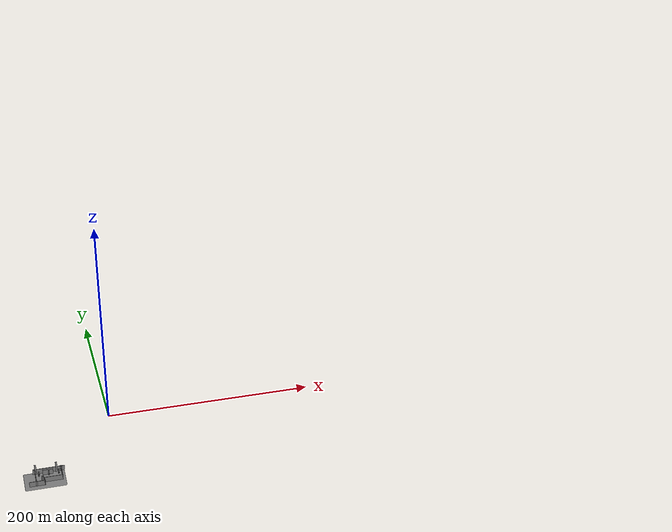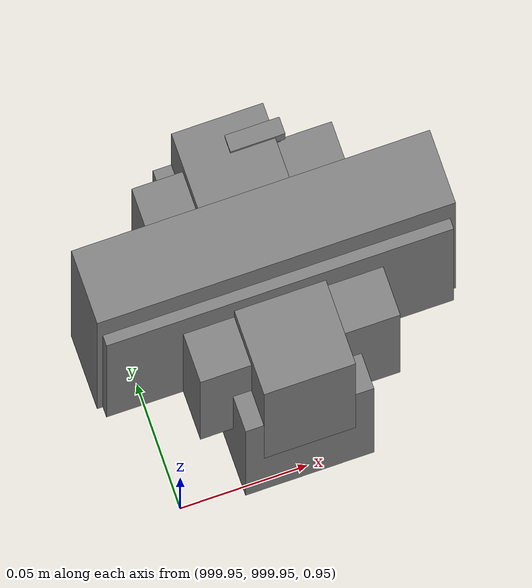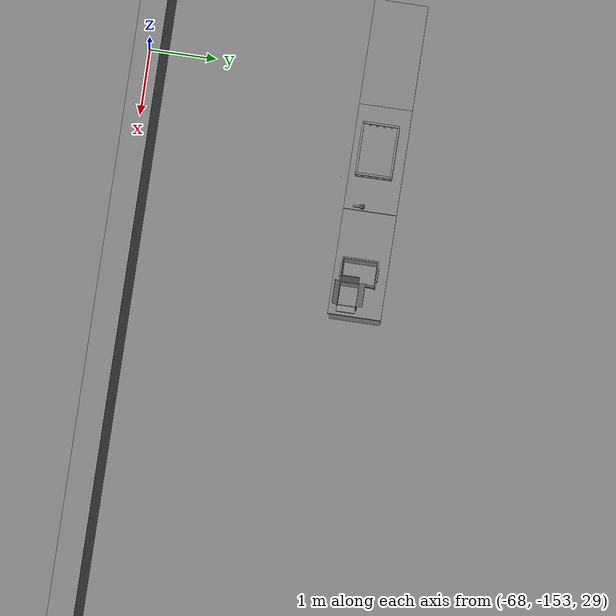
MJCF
<mujoco>
    <option gravity="0.000000000 0.000000000 -9.810000420" timestep="0.0049999999" integrator="implicitfast" density="1.225" viscosity="1.8000001e-05" noslip_iterations="10" iterations="100" sdf_iterations="50">
        <flag multiccd="disable"/>
    </option>
    <size memory="1000M"/>
    <compiler coordinate="local"/>
    <worldbody>
        <light cutoff="30" pos="0 1 1" dir="0 -1 -2"/>
        <light cutoff="30" pos="0 -1 1" dir="0 1 -2"/>
        <body pos="-64.866622925 -149.383972168 30.183746338" euler="89.999984741 89.999946594 0.000000000" name="openloong_gripper_2f85_fix_base_usda_bluebox_01">
            <geom contype="1" conaffinity="1" density="1000" type="box" material="" rgba="0.500000000 0.500000000 0.500000000 1.000000000" solimp="0.899999976 0.949999988 0.001000000" friction="1.000000000 0.005000000 0.000100000" solref="0.020000000 1.000000000" margin="0" condim="3" group="0" pos="0.276580811 0.187225342 0.000068665" quat="0.707106948 0.000077471 0.707106352 0.000077486" size="0.100000001 0.057999998 0.010000000" name="openloong_gripper_2f85_fix_base_usda_geom_FC0CC369_40BE_4097_AA7C_62651A5D2B91"/>
            <geom contype="1" conaffinity="1" density="1000" type="box" material="" rgba="0.500000000 0.500000000 0.500000000 1.000000000" solimp="0.899999976 0.949999988 0.001000000" friction="1.000000000 0.005000000 0.000100000" solref="0.020000000 1.000000000" margin="0" condim="3" group="0" pos="0.000000000 0.002883911 0.000000000" quat="0.999999881 0.000000000 0.000000000 0.000000000" size="0.254000008 0.003000000 0.172000006" name="openloong_gripper_2f85_fix_base_usda_geom_0EDDB1C2_B91C_43C8_8E7B_266CA053DFFB"/>
            <geom contype="1" conaffinity="1" density="1000" type="box" material="" rgba="0.500000000 0.500000000 0.500000000 1.000000000" solimp="0.899999976 0.949999988 0.001000000" friction="1.000000000 0.005000000 0.000100000" solref="0.020000000 1.000000000" margin="0" condim="3" group="0" pos="0.000000000 0.124874115 0.173484802" quat="0.999796331 0.020176515 -0.000000015 0.000000030" size="0.259999990 0.119999997 0.007000000" name="openloong_gripper_2f85_fix_base_usda_geom_135D197A_1B7A_42A9_ACE6_5455493252D2"/>
            <geom contype="1" conaffinity="1" density="1000" type="box" material="" rgba="0.500000000 0.500000000 0.500000000 1.000000000" solimp="0.899999976 0.949999988 0.001000000" friction="1.000000000 0.005000000 0.000100000" solref="0.020000000 1.000000000" margin="0" condim="3" group="0" pos="0.000000000 0.124874115 -0.173469543" quat="0.999796331 -0.020176545 -0.000000015 0.000000000" size="0.259999990 0.119999997 0.007000000" name="openloong_gripper_2f85_fix_base_usda_geom_7CB5E110_2BCA_444B_B40A_6F7299CD5583"/>
            <geom contype="1" conaffinity="1" density="1000" type="box" material="" rgba="0.500000000 0.500000000 0.500000000 1.000000000" solimp="0.899999976 0.949999988 0.001000000" friction="1.000000000 0.005000000 0.000100000" solref="0.020000000 1.000000000" margin="0" condim="3" group="0" pos="0.000000000 0.214008331 0.188980103" quat="0.999912977 0.013176724 0.000000015 0.000000000" size="0.259999990 0.029999999 0.012500000" name="openloong_gripper_2f85_fix_base_usda_geom_3AC1B49B_4554_4397_A4EB_D3004BAF6D1F"/>
            <geom contype="1" conaffinity="1" density="1000" type="box" material="" rgba="0.500000000 0.500000000 0.500000000 1.000000000" solimp="0.899999976 0.949999988 0.001000000" friction="1.000000000 0.005000000 0.000100000" solref="0.020000000 1.000000000" margin="0" condim="3" group="0" pos="-0.258361816 0.125289917 0.001876831" quat="0.702796936 -0.020792112 0.710783124 0.020769298" size="0.189999998 0.119999997 0.009000000" name="openloong_gripper_2f85_fix_base_usda_geom_1BFC0CBF_32CB_4498_9389_6A30466C7953"/>
            <geom contype="1" conaffinity="1" density="1000" type="box" material="" rgba="0.500000000 0.500000000 0.500000000 1.000000000" solimp="0.899999976 0.949999988 0.001000000" friction="1.000000000 0.005000000 0.000100000" solref="0.020000000 1.000000000" margin="0" condim="3" group="0" pos="0.000000000 0.214008331 -0.188980103" quat="0.999912977 -0.013176769 0.000000030 0.000000015" size="0.259999990 0.029999999 0.012500000" name="openloong_gripper_2f85_fix_base_usda_geom_3CC2CAAB_047D_4DE0_85C6_7244DC57E257"/>
            <geom contype="1" conaffinity="1" density="1000" type="box" material="" rgba="0.500000000 0.500000000 0.500000000 1.000000000" solimp="0.899999976 0.949999988 0.001000000" friction="1.000000000 0.005000000 0.000100000" solref="0.020000000 1.000000000" margin="0" condim="3" group="0" pos="-0.276611328 0.187225342 0.000068665" quat="0.707106650 0.000077441 0.707106709 0.000077456" size="0.100000001 0.057999998 0.010000000" name="openloong_gripper_2f85_fix_base_usda_geom_511469A8_5B7C_4E36_B47D_287B7BA69F7E"/>
            <geom contype="1" conaffinity="1" density="1000" type="box" material="" rgba="0.500000000 0.500000000 0.500000000 1.000000000" solimp="0.899999976 0.949999988 0.001000000" friction="1.000000000 0.005000000 0.000100000" solref="0.020000000 1.000000000" margin="0" condim="3" group="0" pos="0.258331299 0.125289917 0.001876831" quat="0.702851415 0.018856421 0.710823774 -0.019329369" size="0.189999998 0.119999997 0.009000000" name="openloong_gripper_2f85_fix_base_usda_geom_23721B05_385E_4BF5_B8D2_D3CEC1E43EB8"/>
            <freejoint name="openloong_gripper_2f85_fix_base_usda_bluebox_01_joint"/>
            <site size="0.005000000 0.005000000 0.005000000" rgba="0.500000000 0.500000000 0.500000000 1.000000000" pos="0.000000000 0.000000000 0.000000000" quat="0.999961913 0.008726534 0.000000000 0.000000000" group="0" type="sphere" name="openloong_gripper_2f85_fix_base_usda_bluebox_01site"/>
        </body>
        <body pos="-64.496299744 -149.491867065 30.235729218" euler="0.000000000 0.000000000 89.999946594" name="openloong_gripper_2f85_fix_base_usda_cardboardbox_01">
            <geom contype="1" conaffinity="1" density="1000" type="box" material="" rgba="0.500000000 0.500000000 0.500000000 1.000000000" solimp="0.899999976 0.949999988 0.001000000" friction="1.000000000 0.005000000 0.000100000" solref="0.020000000 1.000000000" margin="0" condim="3" group="0" pos="-0.003166199 -0.004086494 0.005052090" quat="1.000000000 0.000000000 0.000000000 0.000000000" size="0.142499998 0.177500010 0.005000000" name="openloong_gripper_2f85_fix_base_usda_geom_1DFDF9E9_F7AB_4DC9_A775_E17F163C6815"/>
            <geom contype="1" conaffinity="1" density="1000" type="box" material="" rgba="0.500000000 0.500000000 0.500000000 1.000000000" solimp="0.899999976 0.949999988 0.001000000" friction="1.000000000 0.005000000 0.000100000" solref="0.020000000 1.000000000" margin="0" condim="3" group="0" pos="-0.003166199 0.170316696 0.150570869" quat="1.000000000 0.000000000 0.000000000 0.000000000" size="0.142499998 0.005000000 0.149999991" name="openloong_gripper_2f85_fix_base_usda_geom_173DE1B1_E077_4558_9A0F_6EF35EB8F9F5"/>
            <geom contype="1" conaffinity="1" density="1000" type="box" material="" rgba="0.500000000 0.500000000 0.500000000 1.000000000" solimp="0.899999976 0.949999988 0.001000000" friction="1.000000000 0.005000000 0.000100000" solref="0.020000000 1.000000000" margin="0" condim="3" group="0" pos="-0.147399902 -0.005307198 0.150570869" quat="1.000000000 0.000000000 0.000000000 0.000000000" size="0.005000000 0.177500010 0.149999991" name="openloong_gripper_2f85_fix_base_usda_geom_A50F6049_E96E_47C9_ABAA_F17B94E33A83"/>
            <geom contype="1" conaffinity="1" density="1000" type="box" material="" rgba="0.500000000 0.500000000 0.500000000 1.000000000" solimp="0.899999976 0.949999988 0.001000000" friction="1.000000000 0.005000000 0.000100000" solref="0.020000000 1.000000000" margin="0" condim="3" group="0" pos="0.140275955 -0.005307198 0.150570869" quat="1.000000000 0.000000000 0.000000000 0.000000000" size="0.005000000 0.177500010 0.149999991" name="openloong_gripper_2f85_fix_base_usda_geom_22448E96_F3EC_48F1_A6B7_B64900AFA732"/>
            <geom contype="1" conaffinity="1" density="1000" type="box" material="" rgba="0.500000000 0.500000000 0.500000000 1.000000000" solimp="0.899999976 0.949999988 0.001000000" friction="1.000000000 0.005000000 0.000100000" solref="0.020000000 1.000000000" margin="0" condim="3" group="0" pos="-0.003166199 -0.181550980 0.150570869" quat="1.000000000 0.000000000 0.000000000 0.000000000" size="0.142499998 0.005000000 0.149999991" name="openloong_gripper_2f85_fix_base_usda_geom_FF99A981_AE32_4037_8467_B34B92791930"/>
            <freejoint name="openloong_gripper_2f85_fix_base_usda_cardboardbox_01_joint"/>
            <site size="0.005000000 0.005000000 0.005000000" rgba="0.500000000 0.500000000 0.500000000 1.000000000" pos="0.000000000 0.000000000 0.000000000" quat="0.999961913 0.008726535 0.000000000 0.000000000" group="0" type="sphere" name="openloong_gripper_2f85_fix_base_usda_site_69AE16CC_D37F_4582_911D_735791CBFC52"/>
            <body pos="0.139160156 -0.004048347 0.301930904" euler="-179.999954224 49.383502960 179.999954224" name="openloong_gripper_2f85_fix_base_usda_A1_006">
                <geom contype="1" conaffinity="1" density="1000" type="box" material="" rgba="0.500000000 0.500000000 0.500000000 1.000000000" solimp="0.899999976 0.949999988 0.001000000" friction="1.000000000 0.005000000 0.000100000" solref="0.020000000 1.000000000" margin="0" condim="3" group="0" pos="-0.071587563 0.000009537 0.001745224" quat="0.999999881 0.000000000 0.000000000 0.000000000" size="0.071249999 0.179999992 0.002500000" name="openloong_gripper_2f85_fix_base_usda_geom_80F19A94_D56E_424F_9CBA_90C4E92DEE5F"/>
                <joint armature="0" stiffness="0.07" damping="0.0099999998" axis="0.000000 1.000000 0.000000" type="hinge" name="openloong_gripper_2f85_fix_base_usda_A1_006"/>
            </body>
            <body pos="-0.145902634 -0.004086494 0.301938057" euler="-180.000000000 -60.000011444 -180.000000000" name="openloong_gripper_2f85_fix_base_usda_A2_006">
                <geom contype="1" conaffinity="1" density="1000" type="box" material="" rgba="0.500000000 0.500000000 0.500000000 1.000000000" solimp="0.899999976 0.949999988 0.001000000" friction="1.000000000 0.005000000 0.000100000" solref="0.020000000 1.000000000" margin="0" condim="3" group="0" pos="0.071268082 0.000009537 0.002717972" quat="0.000002921 0.000000000 -0.000000030 0.999999881" size="0.071249999 0.179999992 0.002500000" name="openloong_gripper_2f85_fix_base_usda_geom_2D3ADE18_625E_4EC5_ACB4_45CF82A3A86B"/>
                <joint armature="0" stiffness="0.07" damping="0.0099999998" axis="0.000000 1.000000 0.000000" type="hinge" name="openloong_gripper_2f85_fix_base_usda_A2_006"/>
            </body>
            <body pos="-0.003385544 0.175991058 0.301930904" euler="-125.858116150 -0.000004561 0.000002331" name="openloong_gripper_2f85_fix_base_usda_B2_006">
                <geom contype="1" conaffinity="1" density="1000" type="box" material="" rgba="0.500000000 0.500000000 0.500000000 1.000000000" solimp="0.899999976 0.949999988 0.001000000" friction="1.000000000 0.005000000 0.000100000" solref="0.020000000 1.000000000" margin="0" condim="3" group="0" pos="0.000009537 -0.070939064 -0.002470016" quat="0.999614120 0.027776197 -0.000000015 0.000000030" size="0.137500003 0.064999998 0.005000000" name="openloong_gripper_2f85_fix_base_usda_geom_1CB481A1_9D06_4C8E_A588_B1A6F631C1F6"/>
                <joint armature="0" stiffness="0.07" damping="0.0099999998" axis="1.000000 0.000000 0.000000" type="hinge" name="openloong_gripper_2f85_fix_base_usda_B2_006"/>
            </body>
            <body pos="-0.003385544 -0.184140205 0.301938057" euler="147.805557251 0.000000000 0.000000000" name="openloong_gripper_2f85_fix_base_usda_B1_006">
                <geom contype="1" conaffinity="1" density="1000" type="box" material="" rgba="0.500000000 0.500000000 0.500000000 1.000000000" solimp="0.899999976 0.949999988 0.001000000" friction="1.000000000 0.005000000 0.000100000" solref="0.020000000 1.000000000" margin="0" condim="3" group="0" pos="-0.000028610 0.070202351 -0.002703667" quat="0.999614179 -0.027776167 0.000000000 0.000000000" size="0.137500003 0.064999998 0.005000000" name="openloong_gripper_2f85_fix_base_usda_geom_67978607_DDF7_4C6B_A38F_B694A5C9A737"/>
                <joint armature="0" stiffness="0.07" damping="0.0099999998" axis="1.000000 0.000000 0.000000" type="hinge" name="openloong_gripper_2f85_fix_base_usda_B1_006"/>
            </body>
        </body>
        <body pos="-65.882858276 -149.481979370 30.229999542" euler="-64.487716675 0.000000000 0.000000000" name="openloong_gripper_2f85_fix_base_usda_Barcode">
            <geom contype="1" conaffinity="1" density="1000" type="box" material="" rgba="0.500000000 0.500000000 0.500000000 1.000000000" solimp="0.899999976 0.949999988 0.001000000" friction="1.000000000 0.005000000 0.000100000" solref="0.020000000 1.000000000" margin="0" condim="3" group="0" pos="0.000000000 0.013038635 0.001419067" quat="0.000000000 0.000000000 0.000000000 1.000000119" size="0.034000002 0.010000000 0.017999999" name="openloong_gripper_2f85_fix_base_usda_geom_825051C7_2FD0_49E2_BCEA_66BF283009F1"/>
            <geom contype="1" conaffinity="1" density="1000" type="box" material="" rgba="0.500000000 0.500000000 0.500000000 1.000000000" solimp="0.899999976 0.949999988 0.001000000" friction="1.000000000 0.005000000 0.000100000" solref="0.020000000 1.000000000" margin="0" condim="3" group="0" pos="0.000000000 -0.035301208 -0.007095337" quat="0.000000000 0.000000000 -0.043619365 0.999048233" size="0.028999999 0.010000000 0.020000000" name="openloong_gripper_2f85_fix_base_usda_geom_C5C34A0F_7EC6_4622_B0C7_FA8100BFABA7"/>
            <geom contype="1" conaffinity="1" density="1000" type="box" material="" rgba="0.500000000 0.500000000 0.500000000 1.000000000" solimp="0.899999976 0.949999988 0.001000000" friction="1.000000000 0.005000000 0.000100000" solref="0.020000000 1.000000000" margin="0" condim="3" group="0" pos="0.000000000 -0.043411255 -0.011749268" quat="0.922262907 0.386563420 0.000000000 0.000000000" size="0.026000001 0.010000000 0.020000000" name="openloong_gripper_2f85_fix_base_usda_geom_6F4E88AA_5853_4CBA_A749_9264C934F79E"/>
            <geom contype="1" conaffinity="1" density="1000" type="box" material="" rgba="0.500000000 0.500000000 0.500000000 1.000000000" solimp="0.899999976 0.949999988 0.001000000" friction="1.000000000 0.005000000 0.000100000" solref="0.020000000 1.000000000" margin="0" condim="3" group="0" pos="0.000000000 -0.016967773 -0.031860352" quat="0.000000000 0.000000000 0.000000000 1.000000119" size="0.008000000 0.010000000 0.013000000" name="openloong_gripper_2f85_fix_base_usda_geom_73055923_0018_49B5_8FC3_92FC541E9C43"/>
            <geom contype="1" conaffinity="1" density="1000" type="box" material="" rgba="0.500000000 0.500000000 0.500000000 1.000000000" solimp="0.899999976 0.949999988 0.001000000" friction="1.000000000 0.005000000 0.000100000" solref="0.020000000 1.000000000" margin="0" condim="3" group="0" pos="0.000000000 -0.001869202 0.000312805" quat="0.953716993 0.300705761 0.000000000 0.000000000" size="0.032000002 0.010000000 0.018999999" name="openloong_gripper_2f85_fix_base_usda_geom_9AB5EABB_3D6D_4C5D_B9BA_EFBF120B3430"/>
            <geom contype="1" conaffinity="1" density="1000" type="box" material="" rgba="0.500000000 0.500000000 0.500000000 1.000000000" solimp="0.899999976 0.949999988 0.001000000" friction="1.000000000 0.005000000 0.000100000" solref="0.020000000 1.000000000" margin="0" condim="3" group="0" pos="0.000000000 -0.019531250 -0.003173828" quat="0.953716993 0.300705761 0.000000000 0.000000000" size="0.030999999 0.010000000 0.020000000" name="openloong_gripper_2f85_fix_base_usda_geom_FF045C53_A876_404F_A4D6_41BE15AC687E"/>
            <geom contype="1" conaffinity="1" density="1000" type="box" material="" rgba="0.500000000 0.500000000 0.500000000 1.000000000" solimp="0.899999976 0.949999988 0.001000000" friction="1.000000000 0.005000000 0.000100000" solref="0.020000000 1.000000000" margin="0" condim="3" group="0" pos="0.000000000 -0.035301208 -0.007095337" quat="0.953716993 0.300705761 0.000000000 0.000000000" size="0.028999999 0.010000000 0.020000000" name="openloong_gripper_2f85_fix_base_usda_geom_B4C84883_80DD_4E40_A313_3C7FA3247DF1"/>
            <geom contype="1" conaffinity="1" density="1000" type="box" material="" rgba="0.500000000 0.500000000 0.500000000 1.000000000" solimp="0.899999976 0.949999988 0.001000000" friction="1.000000000 0.005000000 0.000100000" solref="0.020000000 1.000000000" margin="0" condim="3" group="0" pos="0.000000000 -0.042617798 -0.071121216" quat="0.000000000 0.000000000 0.000000000 1.000000119" size="0.013000000 0.021000000 0.059999999" name="openloong_gripper_2f85_fix_base_usda_geom_54091F3B_8327_470D_ABC3_76ABB7C3BBCE"/>
            <freejoint name="openloong_gripper_2f85_fix_base_usda_Barcode_joint"/>
            <site size="0.005000000 0.005000000 0.005000000" rgba="0.500000000 0.500000000 0.500000000 1.000000000" pos="0.000000000 0.000000000 0.000000000" quat="1.000000000 0.000000000 0.000000000 0.000000000" group="0" type="sphere" name="openloong_gripper_2f85_fix_base_usda_Barcode_site"/>
        </body>
        <body pos="-66.745018005 -149.392349243 30.184000015" euler="0.000000000 0.000000000 89.999946594" name="[22333682945848]_Basket_01">
            <geom contype="1" conaffinity="1" density="1000" type="box" material="" rgba="0.500000000 0.500000000 0.500000000 1.000000000" solimp="0.899999976 0.949999988 0.001000000" friction="1.000000000 0.005000000 0.000100000" solref="0.020000000 1.000000000" margin="0" condim="3" group="0" pos="-0.052425385 0.389207840 0.089787483" quat="0.707107008 0.000000000 0.000000000 0.707106411" size="0.014249999 0.014249999 0.059999999" name="[22333682945848]_geom_58B7376E_F894_47AA_A6A8_016E2916E296"/>
            <geom contype="1" conaffinity="1" density="1000" type="box" material="" rgba="0.500000000 0.500000000 0.500000000 1.000000000" solimp="0.899999976 0.949999988 0.001000000" friction="1.000000000 0.005000000 0.000100000" solref="0.020000000 1.000000000" margin="0" condim="3" group="0" pos="0.264015198 -0.133043289 0.089787483" quat="0.707107008 0.000000000 0.000000000 0.707106411" size="0.014249999 0.014249999 0.059999999" name="[22333682945848]_geom_362C9034_5746_48E2_B10E_0A488131D7C2"/>
            <geom contype="1" conaffinity="1" density="1000" type="box" material="" rgba="0.500000000 0.500000000 0.500000000 1.000000000" solimp="0.899999976 0.949999988 0.001000000" friction="1.000000000 0.005000000 0.000100000" solref="0.020000000 1.000000000" margin="0" condim="3" group="0" pos="-0.264015198 -0.265548706 0.089793205" quat="0.707107008 0.000000000 0.000000000 0.707106411" size="0.014249999 0.014249999 0.059999999" name="[22333682945848]_geom_8620507F_4A96_41F5_87BE_9AFE72A0EAD8"/>
            <geom contype="1" conaffinity="1" density="1000" type="box" material="" rgba="0.500000000 0.500000000 0.500000000 1.000000000" solimp="0.899999976 0.949999988 0.001000000" friction="1.000000000 0.005000000 0.000100000" solref="0.020000000 1.000000000" margin="0" condim="3" group="0" pos="-0.160263062 -0.389322281 0.089793205" quat="0.707107008 0.000000000 0.000000000 0.707106411" size="0.014249999 0.014249999 0.059999999" name="[22333682945848]_geom_7E60DCFA_08D7_434F_A93E_F962FB9942A1"/>
            <geom contype="1" conaffinity="1" density="1000" type="box" material="" rgba="0.500000000 0.500000000 0.500000000 1.000000000" solimp="0.899999976 0.949999988 0.001000000" friction="1.000000000 0.005000000 0.000100000" solref="0.020000000 1.000000000" margin="0" condim="3" group="0" pos="0.162265778 -0.389322281 0.089787483" quat="0.707107008 0.000000000 0.000000000 0.707106411" size="0.014249999 0.014249999 0.059999999" name="[22333682945848]_geom_32BAD224_F3DE_4E41_A6C4_15172F4F3530"/>
            <geom contype="1" conaffinity="1" density="1000" type="box" material="" rgba="0.500000000 0.500000000 0.500000000 1.000000000" solimp="0.899999976 0.949999988 0.001000000" friction="1.000000000 0.005000000 0.000100000" solref="0.020000000 1.000000000" margin="0" condim="3" group="0" pos="0.264015198 0.389207840 0.089787483" quat="0.707107008 0.000000000 0.000000000 0.707106411" size="0.014249999 0.014249999 0.059999999" name="[22333682945848]_geom_28B0102F_B242_4B71_950C_D4CCB67745A3"/>
            <geom contype="1" conaffinity="1" density="1000" type="box" material="" rgba="0.500000000 0.500000000 0.500000000 1.000000000" solimp="0.899999976 0.949999988 0.001000000" friction="1.000000000 0.005000000 0.000100000" solref="0.020000000 1.000000000" margin="0" condim="3" group="0" pos="-0.264015198 -0.133043289 0.089793205" quat="0.707107008 0.000000000 0.000000000 0.707106411" size="0.014249999 0.014249999 0.059999999" name="[22333682945848]_geom_0781C2F2_2702_4964_B6D9_493DF43FFCF4"/>
            <geom contype="1" conaffinity="1" density="1000" type="box" material="" rgba="0.500000000 0.500000000 0.500000000 1.000000000" solimp="0.899999976 0.949999988 0.001000000" friction="1.000000000 0.005000000 0.000100000" solref="0.020000000 1.000000000" margin="0" condim="3" group="0" pos="-0.264026642 0.269256592 0.089793205" quat="0.707107008 0.000000000 0.000000000 0.707106411" size="0.014249999 0.014249999 0.059999999" name="[22333682945848]_geom_3315137E_4F09_4459_BE33_4DE716753AFD"/>
            <geom contype="1" conaffinity="1" density="1000" type="box" material="" rgba="0.500000000 0.500000000 0.500000000 1.000000000" solimp="0.899999976 0.949999988 0.001000000" friction="1.000000000 0.005000000 0.000100000" solref="0.020000000 1.000000000" margin="0" condim="3" group="0" pos="0.054462433 0.389207840 0.089787483" quat="0.707107008 0.000000000 0.000000000 0.707106411" size="0.014249999 0.014249999 0.059999999" name="[22333682945848]_geom_884A299B_4D56_4D21_B404_FC7142C0867D"/>
            <geom contype="1" conaffinity="1" density="1000" type="box" material="" rgba="0.500000000 0.500000000 0.500000000 1.000000000" solimp="0.899999976 0.949999988 0.001000000" friction="1.000000000 0.005000000 0.000100000" solref="0.020000000 1.000000000" margin="0" condim="3" group="0" pos="0.054462433 -0.389322281 0.089787483" quat="0.707107008 0.000000000 0.000000000 0.707106411" size="0.014249999 0.014249999 0.059999999" name="[22333682945848]_geom_0CFC7067_E569_42BB_8BAC_0BEF193DF2CD"/>
            <geom contype="1" conaffinity="1" density="1000" type="box" material="" rgba="0.500000000 0.500000000 0.500000000 1.000000000" solimp="0.899999976 0.949999988 0.001000000" friction="1.000000000 0.005000000 0.000100000" solref="0.020000000 1.000000000" margin="0" condim="3" group="0" pos="0.264015198 0.269256592 0.089793205" quat="0.707107008 0.000000000 0.000000000 0.707106411" size="0.014249999 0.014249999 0.059999999" name="[22333682945848]_geom_C29D5C20_7287_4FE1_8872_9B5BAC1F3339"/>
            <geom contype="1" conaffinity="1" density="1000" type="box" material="" rgba="0.500000000 0.500000000 0.500000000 1.000000000" solimp="0.899999976 0.949999988 0.001000000" friction="1.000000000 0.005000000 0.000100000" solref="0.020000000 1.000000000" margin="0" condim="3" group="0" pos="0.264015198 -0.389322281 0.089787483" quat="0.707107008 0.000000000 0.000000000 0.707106411" size="0.014249999 0.014249999 0.059999999" name="[22333682945848]_geom_1AFD614B_7B17_415F_B627_02B85510E066"/>
            <geom contype="1" conaffinity="1" density="1000" type="box" material="" rgba="0.500000000 0.500000000 0.500000000 1.000000000" solimp="0.899999976 0.949999988 0.001000000" friction="1.000000000 0.005000000 0.000100000" solref="0.020000000 1.000000000" margin="0" condim="3" group="0" pos="0.000000000 0.000000000 0.015998840" quat="0.707107008 0.000000000 0.000000000 0.707106411" size="0.403499991 0.279000014 0.015750000" name="[22333682945848]_geom_8DCF6E1C_2EA8_4839_A5C2_80C0E3968A83"/>
            <geom contype="1" conaffinity="1" density="1000" type="box" material="" rgba="0.500000000 0.500000000 0.500000000 1.000000000" solimp="0.899999976 0.949999988 0.001000000" friction="1.000000000 0.005000000 0.000100000" solref="0.020000000 1.000000000" margin="0" condim="3" group="0" pos="0.000000000 -0.389476776 0.163619041" quat="0.707107008 0.000000000 0.000000000 0.707106411" size="0.015000000 0.277500004 0.015750000" name="[22333682945848]_geom_8B70BEBD_139E_4081_A576_FC2DD81A9D5E"/>
            <geom contype="1" conaffinity="1" density="1000" type="box" material="" rgba="0.500000000 0.500000000 0.500000000 1.000000000" solimp="0.899999976 0.949999988 0.001000000" friction="1.000000000 0.005000000 0.000100000" solref="0.020000000 1.000000000" margin="0" condim="3" group="0" pos="0.162265778 0.389207840 0.089787483" quat="0.707107008 0.000000000 0.000000000 0.707106411" size="0.014249999 0.014249999 0.059999999" name="[22333682945848]_geom_ACCB6A53_5109_4947_95A8_25FDB43363F9"/>
            <geom contype="1" conaffinity="1" density="1000" type="box" material="" rgba="0.500000000 0.500000000 0.500000000 1.000000000" solimp="0.899999976 0.949999988 0.001000000" friction="1.000000000 0.005000000 0.000100000" solref="0.020000000 1.000000000" margin="0" condim="3" group="0" pos="0.000000000 0.389471054 0.163619041" quat="0.707107008 0.000000000 0.000000000 0.707106411" size="0.015000000 0.277500004 0.015750000" name="[22333682945848]_geom_BEA00F88_99A2_468C_99AF_9641F373FC2A"/>
            <geom contype="1" conaffinity="1" density="1000" type="box" material="" rgba="0.500000000 0.500000000 0.500000000 1.000000000" solimp="0.899999976 0.949999988 0.001000000" friction="1.000000000 0.005000000 0.000100000" solref="0.020000000 1.000000000" margin="0" condim="3" group="0" pos="-0.263511658 0.000000000 0.163619041" quat="0.707107008 0.000000000 0.000000000 0.707106411" size="0.403499991 0.015000000 0.015750000" name="[22333682945848]_geom_5ECA14C9_D2B2_46CE_8AE2_3A7EDA1A702D"/>
            <geom contype="1" conaffinity="1" density="1000" type="box" material="" rgba="0.500000000 0.500000000 0.500000000 1.000000000" solimp="0.899999976 0.949999988 0.001000000" friction="1.000000000 0.005000000 0.000100000" solref="0.020000000 1.000000000" margin="0" condim="3" group="0" pos="-0.264015198 0.141334534 0.089793205" quat="0.707107008 0.000000000 0.000000000 0.707106411" size="0.014249999 0.014249999 0.059999999" name="[22333682945848]_geom_ED939A36_5426_4778_B715_3CC7A9E49E79"/>
            <geom contype="1" conaffinity="1" density="1000" type="box" material="" rgba="0.500000000 0.500000000 0.500000000 1.000000000" solimp="0.899999976 0.949999988 0.001000000" friction="1.000000000 0.005000000 0.000100000" solref="0.020000000 1.000000000" margin="0" condim="3" group="0" pos="0.264015198 -0.265548706 0.089787483" quat="0.707107008 0.000000000 0.000000000 0.707106411" size="0.014249999 0.014249999 0.059999999" name="[22333682945848]_geom_DD6D2A78_57E2_4BA8_9389_047D0B51CEED"/>
            <geom contype="1" conaffinity="1" density="1000" type="box" material="" rgba="0.500000000 0.500000000 0.500000000 1.000000000" solimp="0.899999976 0.949999988 0.001000000" friction="1.000000000 0.005000000 0.000100000" solref="0.020000000 1.000000000" margin="0" condim="3" group="0" pos="-0.160263062 0.389207840 0.089787483" quat="0.707107008 0.000000000 0.000000000 0.707106411" size="0.014249999 0.014249999 0.059999999" name="[22333682945848]_geom_3161D935_E1D0_4621_B2D6_F65B86CF8887"/>
            <geom contype="1" conaffinity="1" density="1000" type="box" material="" rgba="0.500000000 0.500000000 0.500000000 1.000000000" solimp="0.899999976 0.949999988 0.001000000" friction="1.000000000 0.005000000 0.000100000" solref="0.020000000 1.000000000" margin="0" condim="3" group="0" pos="-0.052425385 -0.389322281 0.089787483" quat="0.707107008 0.000000000 0.000000000 0.707106411" size="0.014249999 0.014249999 0.059999999" name="[22333682945848]_geom_E2A8E505_1CD6_4469_AF0A_A88EA53760A4"/>
            <geom contype="1" conaffinity="1" density="1000" type="box" material="" rgba="0.500000000 0.500000000 0.500000000 1.000000000" solimp="0.899999976 0.949999988 0.001000000" friction="1.000000000 0.005000000 0.000100000" solref="0.020000000 1.000000000" margin="0" condim="3" group="0" pos="-0.264026642 -0.389322281 0.089793205" quat="0.707107008 0.000000000 0.000000000 0.707106411" size="0.014249999 0.014249999 0.059999999" name="[22333682945848]_geom_958CD648_D432_4C06_A633_A0A925FD0231"/>
            <geom contype="1" conaffinity="1" density="1000" type="box" material="" rgba="0.500000000 0.500000000 0.500000000 1.000000000" solimp="0.899999976 0.949999988 0.001000000" friction="1.000000000 0.005000000 0.000100000" solref="0.020000000 1.000000000" margin="0" condim="3" group="0" pos="0.264015198 0.141334534 0.089787483" quat="0.707107008 0.000000000 0.000000000 0.707106411" size="0.014249999 0.014249999 0.059999999" name="[22333682945848]_geom_1821F26E_C934_44B3_A9E2_7DDC7E2044A1"/>
            <geom contype="1" conaffinity="1" density="1000" type="box" material="" rgba="0.500000000 0.500000000 0.500000000 1.000000000" solimp="0.899999976 0.949999988 0.001000000" friction="1.000000000 0.005000000 0.000100000" solref="0.020000000 1.000000000" margin="0" condim="3" group="0" pos="-0.264015198 0.389207840 0.089793205" quat="0.707107008 0.000000000 0.000000000 0.707106411" size="0.014249999 0.014249999 0.059999999" name="[22333682945848]_geom_E6F746DE_2D10_49A5_9F90_C95F4AECF364"/>
            <geom contype="1" conaffinity="1" density="1000" type="box" material="" rgba="0.500000000 0.500000000 0.500000000 1.000000000" solimp="0.899999976 0.949999988 0.001000000" friction="1.000000000 0.005000000 0.000100000" solref="0.020000000 1.000000000" margin="0" condim="3" group="0" pos="0.264015198 0.004480362 0.089787483" quat="0.707107008 0.000000000 0.000000000 0.707106411" size="0.014249999 0.014249999 0.059999999" name="[22333682945848]_geom_53B0336E_6E6E_4517_AB1C_E77A230FEF49"/>
            <geom contype="1" conaffinity="1" density="1000" type="box" material="" rgba="0.500000000 0.500000000 0.500000000 1.000000000" solimp="0.899999976 0.949999988 0.001000000" friction="1.000000000 0.005000000 0.000100000" solref="0.020000000 1.000000000" margin="0" condim="3" group="0" pos="0.263694763 -0.000011444 0.163619041" quat="0.707107008 0.000000000 0.000000000 0.707106411" size="0.403499991 0.015000000 0.015750000" name="[22333682945848]_geom_662833BB_1D69_4F71_AF1A_15129066AFDC"/>
            <geom contype="1" conaffinity="1" density="1000" type="box" material="" rgba="0.500000000 0.500000000 0.500000000 1.000000000" solimp="0.899999976 0.949999988 0.001000000" friction="1.000000000 0.005000000 0.000100000" solref="0.020000000 1.000000000" margin="0" condim="3" group="0" pos="-0.264015198 0.004480362 0.089793205" quat="0.707107008 0.000000000 0.000000000 0.707106411" size="0.014249999 0.014249999 0.059999999" name="[22333682945848]_geom_50299441_6BD0_4E1A_B8D3_654948F9AEDC"/>
            <freejoint name="[22333682945848]_joint_C0165108_F41D_4B60_BED5_C125FF445ECF"/>
        </body>
        <body pos="0.000000000 0.000000000 0.000000000" euler="0.000000000 0.000000000 0.000000000" name="Static Objects_Static Objects">
            <geom contype="1" conaffinity="1" density="1000" type="box" material="" rgba="0.500000000 0.500000000 0.500000000 1.000000000" solimp="0.899999976 0.949999988 0.001000000" friction="1.000000000 0.005000000 0.000100000" solref="0.020000000 1.000000000" margin="0" condim="3" group="0" pos="-67.544113159 -149.365814209 29.727830887" quat="0.500000417 0.499999970 0.499999553 0.499999970" size="0.381000012 0.319999993 0.041000001" name="Static Objects_geom_82C57E7C_AAD7_4494_A3E9_03800554532F"/>
            <geom contype="1" conaffinity="1" density="1000" type="box" material="" rgba="0.500000000 0.500000000 0.500000000 1.000000000" solimp="0.899999976 0.949999988 0.001000000" friction="1.000000000 0.005000000 0.000100000" solref="0.020000000 1.000000000" margin="0" condim="3" group="0" pos="-68.239501953 -149.365814209 30.086868286" quat="0.500000417 0.499999970 0.499999553 0.499999970" size="0.370999992 0.039500002 0.745000005" name="Static Objects_geom_D7BDD25B_2055_4319_A469_D1AB454E859A"/>
            <geom contype="1" conaffinity="1" density="1000" type="box" material="" rgba="0.500000000 0.500000000 0.500000000 1.000000000" solimp="0.899999976 0.949999988 0.001000000" friction="1.000000000 0.005000000 0.000100000" solref="0.020000000 1.000000000" margin="0" condim="3" group="0" pos="-68.239501953 -149.365814209 30.147235870" quat="0.500000417 0.499999970 0.499999553 0.499999970" size="0.400000006 0.022000000 0.800000012" name="Static Objects_geom_8CFD413D_8008_4C36_9CEF_13392CD397C3"/>
            <geom contype="1" conaffinity="1" density="1000" type="box" material="" rgba="0.500000000 0.500000000 0.500000000 1.000000000" solimp="0.899999976 0.949999988 0.001000000" friction="1.000000000 0.005000000 0.000100000" solref="0.020000000 1.000000000" margin="0" condim="3" group="0" pos="-68.934890747 -149.365814209 29.727830887" quat="0.500000417 0.499999970 0.499999553 0.499999970" size="0.381000012 0.319999993 0.041000001" name="Static Objects_geom_EBCF6793_D83B_44CD_AE0F_5A3AEECD7D1A"/>
            <geom contype="1" conaffinity="1" density="1000" type="box" material="" rgba="0.500000000 0.500000000 0.500000000 1.000000000" solimp="0.899999976 0.949999988 0.001000000" friction="1.000000000 0.005000000 0.000100000" solref="0.020000000 1.000000000" margin="0" condim="3" group="0" pos="-68.239501953 -149.365814209 29.561563492" quat="0.500000417 0.499999970 0.499999553 0.499999970" size="0.020000000 0.022000000 0.660000026" name="Static Objects_geom_C9C5A7B3_2BBF_45E3_9426_DEE3222E0812"/>
            <geom contype="1" conaffinity="1" density="1000" type="box" material="" rgba="0.500000000 0.500000000 0.500000000 1.000000000" solimp="0.899999976 0.949999988 0.001000000" friction="1.000000000 0.005000000 0.000100000" solref="0.020000000 1.000000000" margin="0" condim="3" group="0" pos="-65.945671082 -149.365814209 29.727830887" quat="0.500000417 0.499999970 0.499999553 0.499999970" size="0.381000012 0.319999993 0.041000001" name="Static Objects_geom_6FE56040_7864_498A_8627_D5967E81D6A4"/>
            <geom contype="1" conaffinity="1" density="1000" type="box" material="" rgba="0.500000000 0.500000000 0.500000000 1.000000000" solimp="0.899999976 0.949999988 0.001000000" friction="1.000000000 0.005000000 0.000100000" solref="0.020000000 1.000000000" margin="0" condim="3" group="0" pos="-66.641059875 -149.365814209 30.086868286" quat="0.500000417 0.499999970 0.499999553 0.499999970" size="0.370999992 0.039500002 0.745000005" name="Static Objects_geom_62BA0C8C_2057_4F0C_89F2_08DFECBC6BC2"/>
            <geom contype="1" conaffinity="1" density="1000" type="box" material="" rgba="0.500000000 0.500000000 0.500000000 1.000000000" solimp="0.899999976 0.949999988 0.001000000" friction="1.000000000 0.005000000 0.000100000" solref="0.020000000 1.000000000" margin="0" condim="3" group="0" pos="-66.641059875 -149.365814209 30.147235870" quat="0.500000417 0.499999970 0.499999553 0.499999970" size="0.400000006 0.022000000 0.800000012" name="Static Objects_geom_844BE5B4_1724_4D10_A0FC_5DEAB4DE8471"/>
            <geom contype="1" conaffinity="1" density="1000" type="box" material="" rgba="0.500000000 0.500000000 0.500000000 1.000000000" solimp="0.899999976 0.949999988 0.001000000" friction="1.000000000 0.005000000 0.000100000" solref="0.020000000 1.000000000" margin="0" condim="3" group="0" pos="-67.336448669 -149.365814209 29.727830887" quat="0.500000417 0.499999970 0.499999553 0.499999970" size="0.381000012 0.319999993 0.041000001" name="Static Objects_geom_8982F4F9_F889_46D8_9415_36AC1A37BB33"/>
            <geom contype="1" conaffinity="1" density="1000" type="box" material="" rgba="0.500000000 0.500000000 0.500000000 1.000000000" solimp="0.899999976 0.949999988 0.001000000" friction="1.000000000 0.005000000 0.000100000" solref="0.020000000 1.000000000" margin="0" condim="3" group="0" pos="-66.641059875 -149.365814209 29.561563492" quat="0.500000417 0.499999970 0.499999553 0.499999970" size="0.020000000 0.022000000 0.660000026" name="Static Objects_geom_90FDA0D3_2495_49E3_B4A3_594077D541EE"/>
            <geom contype="1" conaffinity="1" density="1000" type="box" material="" rgba="0.500000000 0.500000000 0.500000000 1.000000000" solimp="0.899999976 0.949999988 0.001000000" friction="1.000000000 0.005000000 0.000100000" solref="0.020000000 1.000000000" margin="0" condim="3" group="0" pos="-64.338577271 -149.365814209 29.727830887" quat="0.500000417 0.499999970 0.499999553 0.499999970" size="0.381000012 0.319999993 0.041000001" name="Static Objects_geom_32E5609D_C51F_4580_AA53_81C17BD36980"/>
            <geom contype="1" conaffinity="1" density="1000" type="box" material="" rgba="0.500000000 0.500000000 0.500000000 1.000000000" solimp="0.899999976 0.949999988 0.001000000" friction="1.000000000 0.005000000 0.000100000" solref="0.020000000 1.000000000" margin="0" condim="3" group="0" pos="-65.033966064 -149.365814209 30.086868286" quat="0.500000417 0.499999970 0.499999553 0.499999970" size="0.370999992 0.039500002 0.745000005" name="Static Objects_geom_FCD09927_83A0_4204_A997_54DE1AADB81C"/>
            <geom contype="1" conaffinity="1" density="1000" type="box" material="" rgba="0.500000000 0.500000000 0.500000000 1.000000000" solimp="0.899999976 0.949999988 0.001000000" friction="1.000000000 0.005000000 0.000100000" solref="0.020000000 1.000000000" margin="0" condim="3" group="0" pos="-65.033966064 -149.365814209 30.147235870" quat="0.500000417 0.499999970 0.499999553 0.499999970" size="0.400000006 0.022000000 0.800000012" name="Static Objects_geom_5D0C90F2_AFCA_423C_AAC5_8E6CA2BD1397"/>
            <geom contype="1" conaffinity="1" density="1000" type="box" material="" rgba="0.500000000 0.500000000 0.500000000 1.000000000" solimp="0.899999976 0.949999988 0.001000000" friction="1.000000000 0.005000000 0.000100000" solref="0.020000000 1.000000000" margin="0" condim="3" group="0" pos="-65.729354858 -149.365814209 29.727830887" quat="0.500000417 0.499999970 0.499999553 0.499999970" size="0.381000012 0.319999993 0.041000001" name="Static Objects_geom_3A34F7B3_AB44_45FC_BA99_4D361872AAA8"/>
            <geom contype="1" conaffinity="1" density="1000" type="box" material="" rgba="0.500000000 0.500000000 0.500000000 1.000000000" solimp="0.899999976 0.949999988 0.001000000" friction="1.000000000 0.005000000 0.000100000" solref="0.020000000 1.000000000" margin="0" condim="3" group="0" pos="-65.033966064 -149.365814209 29.561563492" quat="0.500000417 0.499999970 0.499999553 0.499999970" size="0.020000000 0.022000000 0.660000026" name="Static Objects_geom_081B1F2C_4055_46EE_9B40_FD48FE9FAE53"/>
            <geom contype="1" conaffinity="1" density="1000" type="box" material="" rgba="0.500000000 0.500000000 0.500000000 1.000000000" solimp="0.899999976 0.949999988 0.001000000" friction="1.000000000 0.005000000 0.000100000" solref="0.020000000 1.000000000" margin="0" condim="3" group="0" pos="-61.754566193 -137.853729248 33.906845093" quat="0.707107067 0.000000000 0.000000000 0.707106471" size="0.759999990 0.759999990 4.500000000" name="Static Objects_geom_6670E987_970B_4EAE_9D60_EBE017CBE610"/>
            <geom contype="1" conaffinity="1" density="1000" type="box" material="" rgba="0.500000000 0.500000000 0.500000000 1.000000000" solimp="0.899999976 0.949999988 0.001000000" friction="1.000000000 0.005000000 0.000100000" solref="0.020000000 1.000000000" margin="0" condim="3" group="0" pos="-57.511135101 -144.927108765 31.707921982" quat="1.000000000 0.000000000 0.000000000 0.000000000" size="0.200000003 8.000000000 2.299999952" name="Static Objects_geom_E55E1B2B_788A_4B9B_AF77_7B554DBCEF95"/>
            <geom contype="1" conaffinity="1" density="1000" type="box" material="" rgba="0.500000000 0.500000000 0.500000000 1.000000000" solimp="0.899999976 0.949999988 0.001000000" friction="1.000000000 0.005000000 0.000100000" solref="0.020000000 1.000000000" margin="0" condim="3" group="0" pos="-80.517646790 -157.574050903 31.688196182" quat="0.707107067 0.000000000 0.000000000 0.707106471" size="0.600000024 0.600000024 2.299999952" name="Static Objects_geom_1C13D5BF_7950_40E1_B89C_DC2874CF57F6"/>
            <geom contype="1" conaffinity="1" density="1000" type="box" material="" rgba="0.500000000 0.500000000 0.500000000 1.000000000" solimp="0.899999976 0.949999988 0.001000000" friction="1.000000000 0.005000000 0.000100000" solref="0.020000000 1.000000000" margin="0" condim="3" group="0" pos="-80.711044312 -147.414932251 31.666158676" quat="1.000000000 0.000000000 0.000000000 0.000000000" size="0.200000003 10.000000000 2.299999952" name="Static Objects_geom_A13DF754_2CC3_4142_AAF3_C8AD04CDE74A"/>
            <geom contype="1" conaffinity="1" density="1000" type="box" material="" rgba="0.500000000 0.500000000 0.500000000 1.000000000" solimp="0.899999976 0.949999988 0.001000000" friction="1.000000000 0.005000000 0.000100000" solref="0.020000000 1.000000000" margin="0" condim="3" group="0" pos="-57.687217712 -137.434692383 31.688196182" quat="0.707107067 0.000000000 0.000000000 0.707106471" size="0.600000024 0.600000024 2.299999952" name="Static Objects_geom_6EDABEF4_C9F1_4D39_9056_51F4958CCDA2"/>
            <geom contype="1" conaffinity="1" density="1000" type="box" material="" rgba="0.500000000 0.500000000 0.500000000 1.000000000" solimp="0.899999976 0.949999988 0.001000000" friction="1.000000000 0.005000000 0.000100000" solref="0.020000000 1.000000000" margin="0" condim="3" group="0" pos="-69.537033081 -140.263229370 31.714921951" quat="0.707107067 0.000000000 0.000000000 0.707106471" size="0.759999990 4.500000000 2.299999952" name="Static Objects_geom_0A21F272_B860_409C_B980_44EB569A3512"/>
            <geom contype="1" conaffinity="1" density="1000" type="box" material="" rgba="0.500000000 0.500000000 0.500000000 1.000000000" solimp="0.899999976 0.949999988 0.001000000" friction="1.000000000 0.005000000 0.000100000" solref="0.020000000 1.000000000" margin="0" condim="3" group="0" pos="-80.073638916 -137.853713989 33.906845093" quat="0.707107067 0.000000000 0.000000000 0.707106471" size="0.759999990 0.759999990 4.500000000" name="Static Objects_geom_80025DFF_069C_403E_AB2D_FCA5B8662C97"/>
            <geom contype="1" conaffinity="1" density="1000" type="box" material="" rgba="0.500000000 0.500000000 0.500000000 1.000000000" solimp="0.899999976 0.949999988 0.001000000" friction="1.000000000 0.005000000 0.000100000" solref="0.020000000 1.000000000" margin="0" condim="3" group="0" pos="-73.406707764 -155.734664917 31.707921982" quat="1.000000000 0.000000000 0.000000000 0.000000000" size="0.200000003 3.000000000 2.299999952" name="Static Objects_geom_EA3BFB95_895F_4C5B_A19D_9E45FFC55FF4"/>
            <geom contype="1" conaffinity="1" density="1000" type="box" material="" rgba="0.500000000 0.500000000 0.500000000 1.000000000" solimp="0.899999976 0.949999988 0.001000000" friction="1.000000000 0.005000000 0.000100000" solref="0.020000000 1.000000000" margin="0" condim="3" group="0" pos="-68.497543335 -137.448257446 31.707921982" quat="0.707107067 0.000000000 0.000000000 0.707106471" size="0.200000003 14.000000000 2.299999952" name="Static Objects_geom_C50A8782_7023_479B_BE8C_DC24DF73AECE"/>
            <geom contype="1" conaffinity="1" density="1000" type="cylinder" material="" rgba="0.500000000 0.500000000 0.500000000 1.000000000" solimp="0.899999976 0.949999988 0.001000000" friction="1.000000000 0.005000000 0.000100000" solref="0.020000000 1.000000000" margin="0" condim="3" group="0" pos="-68.868522644 -142.134506226 31.711090088" quat="0.707107067 0.000000000 0.000000000 0.707106471" size="0.509999990 2.299999952 1.000000000" name="Static Objects_geom_D581C1BB_537D_42B3_A0FA_D966E2DA0ED3"/>
            <geom contype="1" conaffinity="1" density="1000" type="plane" material="" rgba="0.500000000 0.500000000 0.500000000 1.000000000" solimp="0.899999976 0.949999988 0.001000000" friction="1.000000000 0.005000000 0.000100000" solref="0.020000000 1.000000000" margin="0" condim="3" group="0" pos="-72.873703003 -147.131927490 29.409669876" quat="1.000000000 0.000000000 0.000000000 0.000000000" size="18.000000000 14.000000000 1.000000000" name="Static Objects_geom_727F9C7E_05C9_45F2_ADB7_B43B3BC3A1C1"/>
            <geom contype="1" conaffinity="1" density="1000" type="box" material="" rgba="0.500000000 0.500000000 0.500000000 1.000000000" solimp="0.899999976 0.949999988 0.001000000" friction="1.000000000 0.005000000 0.000100000" solref="0.020000000 1.000000000" margin="0" condim="3" group="0" pos="-79.943580627 -157.782272339 31.707921982" quat="0.707107067 0.000000000 0.000000000 0.707106471" size="0.200000003 7.000000000 2.299999952" name="Static Objects_geom_E58D6A94_F3A9_4290_B4A6_8ABCCC497DB6"/>
            <geom contype="1" conaffinity="1" density="1000" type="box" material="" rgba="0.500000000 0.500000000 0.500000000 1.000000000" solimp="0.899999976 0.949999988 0.001000000" friction="1.000000000 0.005000000 0.000100000" solref="0.020000000 1.000000000" margin="0" condim="3" group="0" pos="-65.421028137 -152.903442383 31.707921982" quat="0.707107067 0.000000000 0.000000000 0.707106471" size="0.200000003 7.800000191 2.299999952" name="Static Objects_geom_80F4F6F2_6BF7_49E8_8805_943E1A82EEFF"/>
            <geom contype="1" conaffinity="1" density="1000" type="box" material="" rgba="0.500000000 0.500000000 0.500000000 1.000000000" solimp="0.899999976 0.949999988 0.001000000" friction="1.000000000 0.005000000 0.000100000" solref="0.020000000 1.000000000" margin="0" condim="3" group="0" pos="-74.776908875 -149.964416504 31.688196182" quat="1.000000000 0.000000000 0.000000000 0.000000000" size="0.600000024 0.409999996 2.299999952" name="Static Objects_geom_E6B223D0_C644_454B_A20B_1DC6043C3093"/>
            <geom contype="1" conaffinity="1" density="1000" type="cylinder" material="" rgba="0.500000000 0.500000000 0.500000000 1.000000000" solimp="0.899999976 0.949999988 0.001000000" friction="1.000000000 0.005000000 0.000100000" solref="0.020000000 1.000000000" margin="0" condim="3" group="0" pos="-60.161884308 -142.134506226 31.711090088" quat="0.707107067 0.000000000 0.000000000 0.707106471" size="0.509999990 2.299999952 1.000000000" name="Static Objects_geom_57726E92_47CE_49BE_9BA2_FA1F02D083DB"/>
            <geom contype="1" conaffinity="1" density="1000" type="cylinder" material="" rgba="0.500000000 0.500000000 0.500000000 1.000000000" solimp="0.899999976 0.949999988 0.001000000" friction="1.000000000 0.005000000 0.000100000" solref="0.020000000 1.000000000" margin="0" condim="3" group="0" pos="-75.382453918 -149.963455200 31.711090088" quat="0.707107067 0.000000000 0.000000000 0.707106471" size="0.409999996 2.299999952 1.000000000" name="Static Objects_geom_43CD272B_F1E9_4774_B8A2_1A52E90E9816"/>
            <geom contype="1" conaffinity="1" density="1000" type="cylinder" material="" rgba="0.500000000 0.500000000 0.500000000 1.000000000" solimp="0.899999976 0.949999988 0.001000000" friction="1.000000000 0.005000000 0.000100000" solref="0.020000000 1.000000000" margin="0" condim="3" group="0" pos="-74.154960632 -149.963455200 31.711090088" quat="0.707107067 0.000000000 0.000000000 0.707106471" size="0.409999996 2.299999952 1.000000000" name="Static Objects_geom_DE08ECB7_4AF9_4933_BC0B_E7D3B321318E"/>
            <geom contype="1" conaffinity="1" density="1000" type="cylinder" material="" rgba="0.500000000 0.500000000 0.500000000 1.000000000" solimp="0.899999976 0.949999988 0.001000000" friction="1.000000000 0.005000000 0.000100000" solref="0.020000000 1.000000000" margin="0" condim="3" group="0" pos="-77.566612244 -142.134506226 31.711090088" quat="0.707107067 0.000000000 0.000000000 0.707106471" size="0.509999990 2.299999952 1.000000000" name="Static Objects_geom_4C5AE642_D9B1_450B_B393_00FC420D3D91"/>
        </body>
        <body pos="1000.000000000 1000.000000000 1.000000000" euler="0.000000000 0.000000000 180.000000000" name="openloong_gripper_2f85_fix_base_usda_battery_01">
            <geom contype="1" conaffinity="1" density="1000" type="box" material="" rgba="0.500000000 0.500000000 0.500000000 1.000000000" solimp="0.899999976 0.949999988 0.001000000" friction="1.000000000 0.005000000 0.000100000" solref="0.020000000 1.000000000" margin="0" condim="3" group="0" pos="-0.011123657 -0.041940309 0.101691343" quat="1.000000000 0.000000000 0.000000000 0.000000000" size="0.010800000 0.003375000 0.004725000" name="openloong_gripper_2f85_fix_base_usda_geom_8FAC3472_73AC_48DE_A90D_F837ACFDF62C"/>
            <geom contype="1" conaffinity="1" density="1000" type="box" material="" rgba="0.500000000 0.500000000 0.500000000 1.000000000" solimp="0.899999976 0.949999988 0.001000000" friction="1.000000000 0.005000000 0.000100000" solref="0.020000000 1.000000000" margin="0" condim="3" group="0" pos="-0.010876465 -0.044247437 0.047066893" quat="0.998702705 -0.050920475 0.000000000 0.000000000" size="0.009450001 0.002700000 0.024975000" name="openloong_gripper_2f85_fix_base_usda_geom_8DAE2247_EA8F_4F18_8EF0_213D2605B288"/>
            <geom contype="1" conaffinity="1" density="1000" type="box" material="" rgba="0.500000000 0.500000000 0.500000000 1.000000000" solimp="0.899999976 0.949999988 0.001000000" friction="1.000000000 0.005000000 0.000100000" solref="0.020000000 1.000000000" margin="0" condim="3" group="0" pos="-0.001235962 -0.000659180 0.047381196" quat="1.000000000 0.000000000 0.000000000 0.000000000" size="0.039420001 0.039150000 0.047250003" name="openloong_gripper_2f85_fix_base_usda_geom_6561C13C_E79E_4054_A79A_54751C7A5C63"/>
            <geom contype="1" conaffinity="1" density="1000" type="box" material="" rgba="0.500000000 0.500000000 0.500000000 1.000000000" solimp="0.899999976 0.949999988 0.001000000" friction="1.000000000 0.005000000 0.000100000" solref="0.020000000 1.000000000" margin="0" condim="3" group="0" pos="-0.010876465 -0.039138794 0.009851727" quat="1.000000000 0.000000000 0.000000000 0.000000000" size="0.009450001 0.010800000 0.013500000" name="openloong_gripper_2f85_fix_base_usda_geom_4D6EB3AD_3533_4B44_8CE9_27F35760DE03"/>
            <geom contype="1" conaffinity="1" density="1000" type="box" material="" rgba="0.500000000 0.500000000 0.500000000 1.000000000" solimp="0.899999976 0.949999988 0.001000000" friction="1.000000000 0.005000000 0.000100000" solref="0.020000000 1.000000000" margin="0" condim="3" group="0" pos="-0.010876465 -0.041528322 0.071508206" quat="1.000000000 0.000000000 0.000000000 0.000000000" size="0.009450001 0.002700000 0.027000001" name="openloong_gripper_2f85_fix_base_usda_geom_116A0F6F_F882_457F_A720_373341B35836"/>
            <freejoint name="openloong_gripper_2f85_fix_base_usda_battery_01_joint"/>
            <site size="0.005000000 0.005000000 0.005000000" rgba="0.500000000 0.500000000 0.500000000 1.000000000" pos="0.000000000 0.000000000 0.000000000" quat="0.999961913 0.008726500 0.000000000 0.000000000" group="0" type="sphere" name="openloong_gripper_2f85_fix_base_usda_battery_01site"/>
        </body>
        <body pos="-65.919876099 -149.078094482 31.168361664" euler="57.746459961 36.380592346 120.068000793" mocap="true" name="spotlight3_SpotLight"/>
        <body pos="1000.000000000 1000.000000000 1.000000000" euler="0.000000000 0.000000000 180.000000000" name="openloong_gripper_2f85_fix_base_usda_cpu_fan">
            <geom contype="1" conaffinity="1" density="1000" type="box" material="" rgba="0.500000000 0.500000000 0.500000000 1.000000000" solimp="0.899999976 0.949999988 0.001000000" friction="1.000000000 0.005000000 0.000100000" solref="0.020000000 1.000000000" margin="0" condim="3" group="0" pos="0.000000000 0.000000000 0.070034981" quat="0.000000000 0.000000000 0.000000000 1.000000000" size="0.070700005 0.014699999 0.070700005" name="openloong_gripper_2f85_fix_base_usda_geom_0A4A0EE2_689D_478F_BE37_1A5CDA9D28D1"/>
            <freejoint name="openloong_gripper_2f85_fix_base_usda_cpu_fan_joint"/>
            <site size="0.005000000 0.005000000 0.005000000" rgba="0.500000000 0.500000000 0.500000000 1.000000000" pos="0.000000000 0.000000000 0.000000000" quat="0.999961913 0.008726535 0.000000000 0.000000000" group="0" type="sphere" name="openloong_gripper_2f85_fix_base_usda_cpu_fancsite"/>
        </body>
        <body pos="1000.000000000 1000.000000000 1.000000000" euler="0.000000000 0.000000000 180.000000000" name="openloong_gripper_2f85_fix_base_usda_wifi_box">
            <geom contype="1" conaffinity="1" density="1000" type="box" material="" rgba="0.500000000 0.500000000 0.500000000 1.000000000" solimp="0.899999976 0.949999988 0.001000000" friction="1.000000000 0.005000000 0.000100000" solref="0.020000000 1.000000000" margin="0" condim="3" group="0" pos="0.000000000 0.000000000 0.058978677" quat="0.000000000 0.000000047 0.000000000 1.000000000" size="0.068499997 0.018999999 0.059000000" name="openloong_gripper_2f85_fix_base_usda_geom_0916E40B_E408_40ED_9077_A3FD7C33A750"/>
            <freejoint name="openloong_gripper_2f85_fix_base_usda_wifi_box_joint"/>
            <site size="0.005000000 0.005000000 0.005000000" rgba="0.500000000 0.500000000 0.500000000 1.000000000" pos="0.000000000 0.000000000 0.000000000" quat="0.999961913 0.008726500 0.000000000 0.000000000" group="0" type="sphere" name="openloong_gripper_2f85_fix_base_usda_wifi_boxsite"/>
        </body>
        <body pos="-66.111564636 -149.461807251 31.169668198" euler="18.719099045 -36.197521210 42.444042206" mocap="true" name="spotlight6_SpotLight"/>
        <body pos="1000.000000000 1000.000000000 1.000000000" euler="0.000011953 0.000005123 -179.999984741" name="openloong_gripper_2f85_fix_base_usda_intel_box">
            <geom contype="1" conaffinity="1" density="1000" type="box" material="" rgba="0.500000000 0.500000000 0.500000000 1.000000000" solimp="0.899999976 0.949999988 0.001000000" friction="1.000000000 0.005000000 0.000100000" solref="0.020000000 1.000000000" margin="0" condim="3" group="0" pos="0.000000000 -0.000067139 0.000082284" quat="0.707106709 0.000000225 0.000000253 0.707106650" size="0.052800003 0.025300000 0.052800003" name="openloong_gripper_2f85_fix_base_usda_geom_8BD87E0F_3431_4966_B627_15495542E81F"/>
            <freejoint name="openloong_gripper_2f85_fix_base_usda_intel_box_joint"/>
            <site size="0.005000000 0.005000000 0.005000000" rgba="0.500000000 0.500000000 0.500000000 1.000000000" pos="0.000000000 0.000000000 0.000000000" quat="0.999961913 0.008726500 0.000000000 0.000000000" group="0" type="sphere" name="openloong_gripper_2f85_fix_base_usda_intel_boxsite"/>
        </body>
        <body pos="1000.000000000 999.999938965 1.000000000" euler="0.000000000 0.000000000 180.000000000" name="openloong_gripper_2f85_fix_base_usda_intelcore_i5">
            <geom contype="1" conaffinity="1" density="1000" type="box" material="" rgba="0.500000000 0.500000000 0.500000000 1.000000000" solimp="0.899999976 0.949999988 0.001000000" friction="1.000000000 0.005000000 0.000100000" solref="0.020000000 1.000000000" margin="0" condim="3" group="0" pos="0.000000000 0.000000000 0.051722717" quat="0.707106709 0.000000000 0.000000000 -0.707106769" size="0.052800000 0.018080002 0.052800000" name="openloong_gripper_2f85_fix_base_usda_geom_B2DBF195_7395_4279_A360_1951BF5D2B62"/>
            <freejoint name="openloong_gripper_2f85_fix_base_usda_intelcore_i5_joint"/>
            <site size="0.005000000 0.005000000 0.005000000" rgba="0.500000000 0.500000000 0.500000000 1.000000000" pos="0.000000000 0.000000000 0.000000000" quat="0.999961913 0.008726534 0.000000000 0.000000000" group="0" type="sphere" name="openloong_gripper_2f85_fix_base_usda_intelcore_i5site"/>
        </body>
        <body pos="-66.161041260 -149.182403564 31.166709900" euler="-109.601379395 70.511589050 162.586517334" mocap="true" name="spotlight2_SpotLight"/>
        <body pos="-66.291030884 -149.869689941 29.018842697" euler="0.000000000 0.000000000 89.999946594" mocap="true" name="openloong_gripper_2f85_fix_base_usda_leftHandMocap"/>
        <body pos="-66.291030884 -149.869689941 29.018842697" euler="0.000000000 0.000000000 89.999946594" mocap="true" name="openloong_gripper_2f85_fix_base_usda_rightHandMocap"/>
        <body pos="-66.291030884 -149.869689941 30.218843460" euler="0.000000000 0.000000000 89.999946594" name="openloong_gripper_2f85_fix_base_usda_base_link">
            <geom contype="1" conaffinity="1" density="1000" type="mesh" material="" rgba="0.783999979 0.783999979 0.783999979 1.000000000" solimp="0.899999976 0.949999988 0.001000000" friction="1.000000000 0.005000000 0.000100000" solref="0.020000000 1.000000000" margin="0" condim="3" group="3" mesh="base_link" pos="0.000000000 0.000000000 0.000000000" quat="1.000000000 0.000000000 0.000000000 0.000000000" size="1.000000000 1.000000000 1.000000000" name="openloong_gripper_2f85_fix_base_usda__geom_7_663E7D06_83C5_408F_B2B3_488DE37849FC"/>
            <site size="0.005000000 0.005000000 0.005000000" rgba="0.500000000 0.500000000 0.500000000 1.000000000" pos="0.000000000 0.000000000 0.000000000" quat="1.000000000 0.000000000 0.000000000 0.000000000" group="0" type="sphere" name="openloong_gripper_2f85_fix_base_usda_imu"/>
            <inertial mass="22.447001" pos="-0.005664100 -0.001336700 0.238289997" diaginertia="0.374352545 0.277180195 0.220617250" quat="0.999247074 0.035235517 -0.015086859 0.006023135"/>
            <body pos="0.000000000 0.000000000 0.299997330" euler="0.000000000 0.000000000 0.000000000" name="openloong_gripper_2f85_fix_base_usda_dummy_body">
                <geom contype="1" conaffinity="1" density="1000" type="sphere" material="" rgba="0.783999979 0.783999979 0.783999979 1.000000000" solimp="0.899999976 0.949999988 0.001000000" friction="1.000000000 0.005000000 0.000100000" solref="0.020000000 1.000000000" margin="0" condim="3" group="3" pos="0.000000000 0.000000000 0.000000000" quat="1.000000000 0.000000000 0.000000000 0.000000000" size="0.010000000 0.000000000 0.000000000" name="openloong_gripper_2f85_fix_base_usda__geom_8_2D9D0FE9_9AF6_4853_BD3F_BC14005C14E7"/>
                <joint armature="0.0099999998" stiffness="0" damping="0.1" axis="0.000000 0.000000 1.000000" type="hinge" name="openloong_gripper_2f85_fix_base_usda_dummy_joint"/>
                <site size="0.010000000 0.005000000 0.005000000" rgba="0.500000000 0.500000000 0.500000000 1.000000000" pos="0.000000000 0.000000000 0.000000000" quat="1.000000000 0.000000000 0.000000000 0.000000000" group="3" type="sphere" name="openloong_gripper_2f85_fix_base_usda_dummy_site"/>
            </body>
            <body pos="0.009002686 0.000000000 0.406400681" euler="0.000000000 0.000000000 0.000000000" name="openloong_gripper_2f85_fix_base_usda_Link_head_yaw">
                <geom contype="1" conaffinity="1" density="1000" type="mesh" material="" rgba="0.783999979 0.783999979 0.783999979 1.000000000" solimp="0.899999976 0.949999988 0.001000000" friction="1.000000000 0.005000000 0.000100000" solref="0.020000000 1.000000000" margin="0" condim="3" group="3" mesh="Link_head_yaw" pos="0.000000000 0.000000000 0.000000000" quat="1.000000000 0.000000000 0.000000000 0.000000000" size="1.000000000 1.000000000 1.000000000" name="openloong_gripper_2f85_fix_base_usda__geom_10_9296158E_C131_493B_A2F2_50D7CE65D2F7"/>
                <inertial mass="0.84249002" pos="0.000000000 -0.002081400 0.044801001" diaginertia="0.000700588 0.000629000 0.000553812" quat="0.706933022 -0.015675601 0.015677100 0.706933022"/>
                <body pos="0.000000000 -0.034599304 0.048500061" euler="0.000000000 0.000000000 0.000000000" name="openloong_gripper_2f85_fix_base_usda_Link_head_pitch">
                    <geom contype="1" conaffinity="1" density="1000" type="mesh" material="" rgba="0.783999979 0.783999979 0.783999979 1.000000000" solimp="0.899999976 0.949999988 0.001000000" friction="1.000000000 0.005000000 0.000100000" solref="0.020000000 1.000000000" margin="0" condim="3" group="3" mesh="Link_head_pitch" pos="0.000000000 0.000000000 0.000000000" quat="1.000000000 0.000000000 0.000000000 0.000000000" size="1.000000000 1.000000000 1.000000000" name="openloong_gripper_2f85_fix_base_usda__geom_12_91469E17_0286_40B4_82BB_78F439A86A70"/>
                    <inertial mass="1.3943" pos="0.020569000 0.033004001 0.125000000" diaginertia="0.006381400 0.006289940 0.004481460" quat="0.973390222 0.008406822 0.228157058 0.019624906"/>
                    <body pos="0.000000000 0.029998779 0.000000000" euler="0.000000000 0.000000000 0.000000000" name="openloong_gripper_2f85_fix_base_usda_neck_center_body">
                        <site size="0.010000000 0.005000000 0.005000000" rgba="0.500000000 0.500000000 0.500000000 1.000000000" pos="0.000000000 0.000000000 0.000000000" quat="1.000000000 0.000000000 0.000000000 0.000000000" group="3" type="sphere" name="openloong_gripper_2f85_fix_base_usda_neck_center_site"/>
                        <body pos="0.020004272 0.000000000 0.149999619" euler="-0.000002229 39.998176575 -90.000205994" name="openloong_gripper_2f85_fix_base_usda_camera_head">
                            <site size="0.010000000 0.005000000 0.005000000" rgba="0.500000000 0.500000000 0.500000000 1.000000000" pos="0.000000000 0.000000000 0.000000000" quat="1.000000000 0.000000000 0.000000000 0.000000000" group="3" type="sphere" name="openloong_gripper_2f85_fix_base_usda_camera_head_site"/>
                        </body>
                    </body>
                </body>
            </body>
            <body pos="0.003997803 -0.161598206 0.392200470" euler="0.000000000 0.000000000 0.000000000" name="openloong_gripper_2f85_fix_base_usda_Link_arm_r_01">
                <geom contype="1" conaffinity="1" density="1000" type="mesh" material="" rgba="0.783999979 0.783999979 0.783999979 1.000000000" solimp="0.899999976 0.949999988 0.001000000" friction="1.000000000 0.005000000 0.000100000" solref="0.020000000 1.000000000" margin="0" condim="3" group="3" mesh="Link_arm_r_01" pos="0.000000000 0.000000000 0.000000000" quat="1.000000000 0.000000000 0.000000000 0.000000000" size="1.000000000 1.000000000 1.000000000" name="openloong_gripper_2f85_fix_base_usda__geom_14_DA383BD4_75A2_4630_9D11_E8C28EFF9E05"/>
                <joint armature="0.0099999998" stiffness="0" damping="1" axis="0.000000 -1.000000 0.000000" limited="true" range="-170.000015259 170.000015259" type="hinge" name="openloong_gripper_2f85_fix_base_usda_J_arm_r_01"/>
                <inertial mass="0.75641" pos="0.004494600 -0.038293999 -0.000001874" diaginertia="0.000842990 0.000803050 0.000587120" quat="-0.000163502 0.707098067 0.000812463 0.707115054"/>
                <body pos="-0.041992188 -0.041000366 0.000000000" euler="0.000000000 0.000000000 0.000000000" name="openloong_gripper_2f85_fix_base_usda_Link_arm_r_02">
                    <geom contype="1" conaffinity="1" density="1000" type="mesh" material="" rgba="0.783999979 0.783999979 0.783999979 1.000000000" solimp="0.899999976 0.949999988 0.001000000" friction="1.000000000 0.005000000 0.000100000" solref="0.020000000 1.000000000" margin="0" condim="3" group="3" mesh="Link_arm_r_02" pos="0.000000000 0.000000000 0.000000000" quat="1.000000000 0.000000000 0.000000000 0.000000000" size="1.000000000 1.000000000 1.000000000" name="openloong_gripper_2f85_fix_base_usda__geom_16_360AB7C3_30DA_4EA5_8D3D_CBE06F1076F7"/>
                    <joint armature="0.0099999998" stiffness="0" damping="1" axis="-1.000000 0.000000 0.000000" limited="true" range="-105.000244141 105.000244141" type="hinge" name="openloong_gripper_2f85_fix_base_usda_J_arm_r_02"/>
                    <inertial mass="0.98500001" pos="0.041999999 -0.067430697 0.000000000" diaginertia="0.002262690 0.001730990 0.001154020" quat="0.500000000 0.500000000 -0.500000000 0.500000000"/>
                    <body pos="0.041992188 -0.122596741 0.000000000" euler="0.000000000 0.000000000 0.000000000" name="openloong_gripper_2f85_fix_base_usda_Link_arm_r_03">
                        <geom contype="1" conaffinity="1" density="1000" type="mesh" material="" rgba="0.783999979 0.783999979 0.783999979 1.000000000" solimp="0.899999976 0.949999988 0.001000000" friction="1.000000000 0.005000000 0.000100000" solref="0.020000000 1.000000000" margin="0" condim="3" group="3" mesh="Link_arm_r_03" pos="0.000000000 0.000000000 0.000000000" quat="1.000000000 0.000000000 0.000000000 0.000000000" size="1.000000000 1.000000000 1.000000000" name="openloong_gripper_2f85_fix_base_usda__geom_18_1432F84B_6ED7_488A_8FE4_79EF6AA88EF3"/>
                        <joint armature="0.0099999998" stiffness="0" damping="1" axis="0.000000 -1.000000 0.000000" limited="true" range="-170.000015259 170.000015259" type="hinge" name="openloong_gripper_2f85_fix_base_usda_J_arm_r_03"/>
                        <inertial mass="0.95899999" pos="-0.001413580 -0.164663002 0.020757901" diaginertia="0.002101340 0.002064590 0.000754802" quat="0.560480952 0.454391927 -0.443732947 0.531497955"/>
                        <body pos="0.035293579 -0.177406311 0.023998260" euler="0.000000000 0.000000000 0.000000000" name="openloong_gripper_2f85_fix_base_usda_Link_arm_r_04">
                            <geom contype="1" conaffinity="1" density="1000" type="mesh" material="" rgba="0.783999979 0.783999979 0.783999979 1.000000000" solimp="0.899999976 0.949999988 0.001000000" friction="1.000000000 0.005000000 0.000100000" solref="0.020000000 1.000000000" margin="0" condim="3" group="3" mesh="Link_arm_r_04" pos="0.000000000 0.000000000 0.000000000" quat="1.000000000 0.000000000 0.000000000 0.000000000" size="1.000000000 1.000000000 1.000000000" name="openloong_gripper_2f85_fix_base_usda__geom_20_44F1C2A7_5E25_433C_8C0C_C356718AB21A"/>
                            <joint armature="0.0099999998" stiffness="0" damping="1" axis="-1.000000 0.000000 0.000000" limited="true" range="0.000000000 170.000015259" type="hinge" name="openloong_gripper_2f85_fix_base_usda_J_arm_r_04"/>
                            <inertial mass="0.60000002" pos="-0.038727000 -0.060766999 -0.021003000" diaginertia="0.001092610 0.000712422 0.000645102" quat="0.327701002 0.632602990 -0.467366993 0.523443997"/>
                            <body pos="-0.035293579 -0.103492737 -0.023998260" euler="0.000000000 0.000000000 0.000000000" name="openloong_gripper_2f85_fix_base_usda_Link_arm_r_05">
                                <geom contype="1" conaffinity="1" density="1000" type="mesh" material="" rgba="0.783999979 0.783999979 0.783999979 1.000000000" solimp="0.899999976 0.949999988 0.001000000" friction="1.000000000 0.005000000 0.000100000" solref="0.020000000 1.000000000" margin="0" condim="3" group="3" mesh="Link_arm_r_05" pos="0.000000000 0.000000000 0.000000000" quat="1.000000000 0.000000000 0.000000000 0.000000000" size="1.000000000 1.000000000 1.000000000" name="openloong_gripper_2f85_fix_base_usda__geom_22_ED4DDB60_0C8C_41E8_B973_D4A148CB8618"/>
                                <joint armature="0.0099999998" stiffness="0" damping="1" axis="0.000000 -1.000000 0.000000" limited="true" range="-170.000015259 170.000015259" type="hinge" name="openloong_gripper_2f85_fix_base_usda_J_arm_r_05"/>
                                <inertial mass="0.68976003" pos="0.000032712 -0.068658002 -0.000111780" diaginertia="0.002522510 0.002411100 0.000448695" quat="0.707660973 0.706543028 -0.002603360 0.002470550"/>
                                <body pos="-0.026489258 -0.196502686 0.000000000" euler="0.000000000 0.000000000 0.000000000" name="openloong_gripper_2f85_fix_base_usda_Link_arm_r_06">
                                    <geom contype="1" conaffinity="1" density="1000" type="mesh" material="" rgba="0.783999979 0.783999979 0.783999979 1.000000000" solimp="0.899999976 0.949999988 0.001000000" friction="1.000000000 0.005000000 0.000100000" solref="0.020000000 1.000000000" margin="0" condim="3" group="3" mesh="Link_arm_r_06" pos="0.000000000 0.000000000 0.000000000" quat="1.000000000 0.000000000 0.000000000 0.000000000" size="1.000000000 1.000000000 1.000000000" name="openloong_gripper_2f85_fix_base_usda__geom_24_F7935DFE_1AB8_4672_A1F0_FCEAD7EF8DA6"/>
                                    <joint armature="0.0099999998" stiffness="0" damping="1" axis="1.000000 0.000000 0.000000" limited="true" range="-105.000244141 105.000244141" type="hinge" name="openloong_gripper_2f85_fix_base_usda_J_arm_r_06"/>
                                    <inertial mass="0.28" pos="0.026078001 -0.000000896 0.001663700" diaginertia="0.000156930 0.000145601 0.000104979" quat="0.707080841 0.001851080 0.001883810 0.707127810"/>
                                    <body pos="0.026489258 0.000000000 0.031799316" euler="0.000000000 0.000000000 0.000000000" name="openloong_gripper_2f85_fix_base_usda_Link_arm_r_07">
                                        <geom contype="1" conaffinity="1" density="1000" type="mesh" material="" rgba="0.783999979 0.783999979 0.783999979 1.000000000" solimp="0.899999976 0.949999988 0.001000000" friction="1.000000000 0.005000000 0.000100000" solref="0.020000000 1.000000000" margin="0" condim="3" group="3" mesh="Link_arm_r_07" pos="0.000000000 0.000000000 0.000000000" quat="1.000000000 0.000000000 0.000000000 0.000000000" size="1.000000000 1.000000000 1.000000000" name="openloong_gripper_2f85_fix_base_usda__geom_26_113E881B_ACC2_4267_9784_4EADF8C34A94"/>
                                        <joint armature="0.0099999998" stiffness="0" damping="1" axis="0.000000 0.000000 1.000000" limited="true" range="-60.000133514 60.000133514" type="hinge" name="openloong_gripper_2f85_fix_base_usda_J_arm_r_07"/>
                                        <inertial mass="0.61353999" pos="-0.007859000 -0.158170000 -0.027736001" diaginertia="0.003037610 0.002570910 0.000729379" quat="0.427542925 0.443532884 -0.553093910 0.560867906"/>
                                        <body pos="0.000000000 0.286994934 -0.270000458" euler="150.000350952 -0.000001649 -0.000000442" name="openloong_gripper_2f85_fix_base_usda_camera_wrist_r">
                                            <site size="0.010000000 0.005000000 0.005000000" rgba="0.500000000 0.500000000 0.500000000 1.000000000" pos="0.000000000 0.000000000 0.000000000" quat="1.000000000 0.000000000 0.000000000 0.000000000" group="3" type="sphere" name="openloong_gripper_2f85_fix_base_usda_camera_wrist_r_site"/>
                                        </body>
                                        <body pos="0.000000000 -0.220008850 -0.033002853" euler="0.000000000 0.000000000 179.999969482" name="openloong_gripper_2f85_fix_base_usda_ee_center_body_r">
                                            <site size="0.010000000 0.005000000 0.005000000" rgba="0.500000000 0.500000000 0.500000000 1.000000000" pos="0.000000000 0.000000000 0.000000000" quat="1.000000000 0.000000000 0.000000000 0.000000000" group="3" type="sphere" name="openloong_gripper_2f85_fix_base_usda_ee_center_site_r"/>
                                        </body>
                                        <body pos="0.000000000 -0.066001892 -0.031000137" euler="89.999984741 0.000000000 180.000000000" name="openloong_gripper_2f85_fix_base_usda_zbr_base_link">
                                            <geom contype="1" conaffinity="1" density="1000" type="mesh" material="" rgba="0.783999979 0.783999979 0.783999979 1.000000000" solimp="0.899999976 0.949999988 0.001000000" friction="1.000000000 0.005000000 0.000100000" solref="0.020000000 1.000000000" margin="0" condim="3" group="3" mesh="base" pos="0.000000000 0.000003815 -0.000007629" quat="1.000000000 0.000000000 0.000000000 0.000000000" size="1.000000238 1.000000238 1.000000238" name="openloong_gripper_2f85_fix_base_usda__geom_30_F1D2295B_511F_476E_AE4E_1F7AA0D1F106"/>
                                            <inertial mass="0.77744102" pos="0.000000000 -0.000027039 0.035467502" diaginertia="0.000260285 0.000225381 0.000152708" quat="0.999998808 -0.001528488 0.000000000 0.000000000"/>
                                            <body pos="-0.030609138 0.004745484 0.065696731" euler="-89.999984741 -0.000000000 0.000000000" name="openloong_gripper_2f85_fix_base_usda_r_left_driver">
                                                <geom contype="1" conaffinity="1" density="1000" type="mesh" material="" rgba="0.783999979 0.783999979 0.783999979 1.000000000" solimp="0.899999976 0.949999988 0.001000000" friction="1.000000000 0.005000000 0.000100000" solref="0.020000000 1.000000000" margin="0" condim="3" group="3" mesh="driver" pos="0.030609138 0.054901138 -0.004699708" quat="0.707106829 0.707106709 0.000000000 -0.000000000" size="1.000000238 1.000000238 1.000000238" name="openloong_gripper_2f85_fix_base_usda__geom_32_95F3F288_BD6C_4D7F_A5B1_F55B6DA54D97"/>
                                                <joint armature="0.0049999999" stiffness="0" damping="0.1" axis="0.000000 0.000000 1.000000" limited="true" range="0.000000000 51.566200256" type="hinge" name="openloong_gripper_2f85_fix_base_usda_r_left_driver_joint"/>
                                                <inertial mass="0.0089956298" pos="0.000000000 0.017754700 0.001073140" diaginertia="0.000001724 0.000001609 0.000000322" quat="0.681301236 0.732003212 0.000000000 0.000000000"/>
                                                <body pos="-0.031402595 0.004524232 -0.010200503" euler="0.000000000 0.000000000 180.000000000" name="openloong_gripper_2f85_fix_base_usda_r_left_coupler">
                                                    <geom contype="1" conaffinity="1" density="1000" type="mesh" material="" rgba="0.783999979 0.783999979 0.783999979 1.000000000" solimp="0.899999976 0.949999988 0.001000000" friction="1.000000000 0.005000000 0.000100000" solref="0.020000000 1.000000000" margin="0" condim="3" group="3" mesh="coupler" pos="-0.062011734 -0.050354015 0.005500795" quat="0.707106829 -0.707106709 0.000000000 -0.000000000" size="1.000000238 1.000000238 1.000000238" name="openloong_gripper_2f85_fix_base_usda__geom_34_C4702ED9_C75A_4381_9C06_6C238F9ADED0"/>
                                                    <inertial mass="0.0140974" pos="0.000000000 0.003012090 0.023217499" diaginertia="0.000004162 0.000003522 0.000000888" quat="0.705635548 -0.045590367 0.045590367 0.705635548"/>
                                                </body>
                                            </body>
                                            <body pos="-0.012695315 -0.012001040 0.072212234" euler="-89.999984741 -0.000000000 0.000000000" name="openloong_gripper_2f85_fix_base_usda_r_left_spring_link">
                                                <geom contype="1" conaffinity="1" density="1000" type="mesh" material="" rgba="0.783999979 0.783999979 0.783999979 1.000000000" solimp="0.899999976 0.949999988 0.001000000" friction="1.000000000 0.005000000 0.000100000" solref="0.020000000 1.000000000" margin="0" condim="3" group="3" mesh="spring_link" pos="0.012695315 0.061416641 0.012050631" quat="0.707106829 0.707106709 0.000000000 -0.000000000" size="1.000000238 1.000000238 1.000000238" name="openloong_gripper_2f85_fix_base_usda__geom_36_7872E268_9592_4B17_98BC_765E434F2F83"/>
                                                <joint armature="0.001" stiffness="0.050000001" damping="0.00125" axis="0.000000 0.000000 1.000000" limited="true" range="-17.000000000 51.566200256" type="hinge" name="openloong_gripper_2f85_fix_base_usda_r_left_spring_link_joint"/>
                                                <inertial mass="0.0221642" pos="-0.000000009 0.018162400 0.021265799" diaginertia="0.000008969 0.000006717 0.000002639" quat="0.663403213 -0.244737089 0.244737089 0.663403213"/>
                                                <body pos="-0.038208015 -0.042503368 0.002950669" euler="180.000000000 0.000000000 -0.002185660" name="openloong_gripper_2f85_fix_base_usda_r_left_follower">
                                                    <geom contype="1" conaffinity="1" density="1000" type="mesh" material="" rgba="0.783999979 0.783999979 0.783999979 1.000000000" solimp="0.899999976 0.949999988 0.001000000" friction="1.000000000 0.005000000 0.000100000" solref="0.020000000 1.000000000" margin="0" condim="3" group="3" mesh="tongue" pos="0.050918590 -0.103920005 -0.009099962" quat="0.707106829 -0.707106709 0.000000030 0.000000030" size="1.000000238 1.000000238 1.000000238" name="openloong_gripper_2f85_fix_base_usda__geom_40_7BFA9842_032D_4EF0_8750_9DCC4B2CF5FA"/>
                                                    <geom contype="1" conaffinity="1" density="1000" type="mesh" material="" rgba="0.783999979 0.783999979 0.783999979 1.000000000" solimp="0.899999976 0.949999988 0.001000000" friction="1.000000000 0.005000000 0.000100000" solref="0.020000000 1.000000000" margin="0" condim="3" group="3" mesh="follower" pos="0.050918590 -0.103920005 -0.009099962" quat="0.707106829 -0.707106709 0.000000030 0.000000030" size="1.000000238 1.000000238 1.000000238" name="openloong_gripper_2f85_fix_base_usda__geom_39_3021A9B8_4C27_4EA3_AED1_E46C0FE35AA7"/>
                                                    <joint armature="0.001" stiffness="0" damping="0.1" axis="0.000000 0.000000 1.000000" limited="true" range="-49.999961853 51.566200256" type="hinge" name="openloong_gripper_2f85_fix_base_usda_r_left_follower"/>
                                                    <inertial mass="0.0125222" pos="0.000000000 -0.011046000 0.012478600" diaginertia="0.000002674 0.000002456 0.000000602" quat="0.986436546 0.164143041 0.000000000 0.000000000"/>
                                                    <body pos="-0.037765510 -0.103912376 -0.009099962" euler="-89.999984741 0.000000000 0.000004829" name="openloong_gripper_2f85_fix_base_usda_r_left_pad">
                                                        <geom contype="1" conaffinity="1" density="1000" type="box" material="" rgba="0.550000012 0.550000012 0.550000012 1.000000000" solimp="0.949999988 0.990000010 0.001000000" friction="0.699999988 0.005000000 0.000100000" solref="0.020000000 1.000000000" margin="0" condim="3" group="3" mass="1e-06" pos="0.043243419 0.000003815 0.119995147" quat="0.999999881 0.000000000 0.000000000 0.000000000" size="0.002000001 0.011000003 0.009375002" name="openloong_gripper_2f85_fix_base_usda_r_left_pad1_44730FC8_0B5D_4768_9163_5786695D007D"/>
                                                        <geom contype="1" conaffinity="1" density="1000" type="box" material="" rgba="0.449999988 0.449999988 0.449999988 1.000000000" solimp="0.949999988 0.990000010 0.001000000" friction="0.600000024 0.005000000 0.000100000" solref="0.020000000 1.000000000" margin="0" condim="3" group="3" mass="1e-06" pos="0.043243419 0.000003815 0.138748199" quat="0.999999881 0.000000000 0.000000000 0.000000000" size="0.002000001 0.011000003 0.009375002" name="openloong_gripper_2f85_fix_base_usda_r_left_pad2_AD37E865_8A2C_4A8C_8606_FE965CF8CAFD"/>
                                                    </body>
                                                </body>
                                            </body>
                                            <body pos="0.030593880 -0.004753114 0.065696731" euler="89.999984741 0.000000000 180.000000000" name="openloong_gripper_2f85_fix_base_usda_r_right_driver">
                                                <geom contype="1" conaffinity="1" density="1000" type="mesh" material="" rgba="0.783999979 0.783999979 0.783999979 1.000000000" solimp="0.899999976 0.949999988 0.001000000" friction="1.000000000 0.005000000 0.000100000" solref="0.020000000 1.000000000" margin="0" condim="3" group="3" mesh="driver" pos="0.030593880 0.054901138 -0.004699708" quat="0.707106829 0.707106709 0.000000000 0.000000000" size="1.000000238 1.000000238 1.000000238" name="openloong_gripper_2f85_fix_base_usda__geom_42_48B652EA_1E10_4227_B09B_C5C5F186EDD2"/>
                                                <joint armature="0.0049999999" stiffness="0" damping="0.1" axis="0.000000 0.000000 1.000000" limited="true" range="0.000000000 51.566200256" type="hinge" name="openloong_gripper_2f85_fix_base_usda_r_right_driver_joint"/>
                                                <inertial mass="0.0089956298" pos="0.000000000 0.017754700 0.001073140" diaginertia="0.000001724 0.000001609 0.000000322" quat="0.681301236 0.732003212 0.000000000 0.000000000"/>
                                                <body pos="-0.031417854 0.004531861 -0.010202411" euler="0.000000000 0.000000000 180.000000000" name="openloong_gripper_2f85_fix_base_usda_r_right_coupler">
                                                    <geom contype="1" conaffinity="1" density="1000" type="mesh" material="" rgba="0.783999979 0.783999979 0.783999979 1.000000000" solimp="0.899999976 0.949999988 0.001000000" friction="1.000000000 0.005000000 0.000100000" solref="0.020000000 1.000000000" margin="0" condim="3" group="3" mesh="coupler" pos="-0.062042251 -0.050376903 0.005500795" quat="0.707106829 -0.707106709 0.000000000 0.000000000" size="1.000000238 1.000000238 1.000000238" name="openloong_gripper_2f85_fix_base_usda__geom_44_E1D7934B_D665_49C0_BDE8_2414F3A55A16"/>
                                                    <inertial mass="0.0140974" pos="0.000000000 0.003012090 0.023217499" diaginertia="0.000004162 0.000003522 0.000000888" quat="0.705635548 -0.045590367 0.045590367 0.705635548"/>
                                                </body>
                                            </body>
                                            <body pos="0.012695315 0.011997226 0.072219864" euler="89.999984741 0.000000000 180.000000000" name="openloong_gripper_2f85_fix_base_usda_r_right_spring_link">
                                                <geom contype="1" conaffinity="1" density="1000" type="mesh" material="" rgba="0.783999979 0.783999979 0.783999979 1.000000000" solimp="0.899999976 0.949999988 0.001000000" friction="1.000000000 0.005000000 0.000100000" solref="0.020000000 1.000000000" margin="0" condim="3" group="3" mesh="spring_link" pos="0.012695315 0.061424270 0.012048724" quat="0.707106829 0.707106709 0.000000000 0.000000000" size="1.000000238 1.000000238 1.000000238" name="openloong_gripper_2f85_fix_base_usda__geom_46_89C5D91E_5DA6_4452_B242_FB9A7753DF58"/>
                                                <joint armature="0.001" stiffness="0.050000001" damping="0.00125" axis="0.000000 0.000000 1.000000" limited="true" range="-17.000000000 51.566200256" type="hinge" name="openloong_gripper_2f85_fix_base_usda_r_right_spring_link_joint"/>
                                                <inertial mass="0.0221642" pos="-0.000000009 0.018162400 0.021265799" diaginertia="0.000008969 0.000006717 0.000002639" quat="0.663403213 -0.244737089 0.244737089 0.663403213"/>
                                                <body pos="-0.038208015 -0.042495739 0.002950669" euler="180.000000000 0.000000000 0.000000000" name="openloong_gripper_2f85_fix_base_usda_r_right_follower">
                                                    <geom contype="1" conaffinity="1" density="1000" type="mesh" material="" rgba="0.783999979 0.783999979 0.783999979 1.000000000" solimp="0.899999976 0.949999988 0.001000000" friction="1.000000000 0.005000000 0.000100000" solref="0.020000000 1.000000000" margin="0" condim="3" group="3" mesh="follower" pos="0.050888073 -0.103927635 -0.009099962" quat="0.707106829 -0.707106709 0.000000000 0.000000000" size="1.000000238 1.000000238 1.000000238" name="openloong_gripper_2f85_fix_base_usda__geom_50_17AE5DF9_A976_4B15_A54B_08AE5DF8DD5F"/>
                                                    <geom contype="1" conaffinity="1" density="1000" type="mesh" material="" rgba="0.783999979 0.783999979 0.783999979 1.000000000" solimp="0.899999976 0.949999988 0.001000000" friction="1.000000000 0.005000000 0.000100000" solref="0.020000000 1.000000000" margin="0" condim="3" group="3" mesh="tongue" pos="0.050888073 -0.103927635 -0.009099962" quat="0.707106829 -0.707106709 0.000000000 0.000000000" size="1.000000238 1.000000238 1.000000238" name="openloong_gripper_2f85_fix_base_usda__geom_49_964250DD_82B1_4777_97F6_81A1F43693C0"/>
                                                    <joint armature="0.001" stiffness="0" damping="0.1" axis="0.000000 0.000000 1.000000" limited="true" range="-49.999961853 51.566200256" type="hinge" name="openloong_gripper_2f85_fix_base_usda_r_right_follower_joint"/>
                                                    <inertial mass="0.0125222" pos="0.000000000 -0.011046000 0.012478600" diaginertia="0.000002674 0.000002456 0.000000602" quat="0.986436546 0.164143041 0.000000000 0.000000000"/>
                                                    <body pos="-0.037811287 -0.103927635 -0.009099962" euler="-89.999984741 0.000000000 0.000000000" name="openloong_gripper_2f85_fix_base_usda_r_right_pad">
                                                        <geom contype="1" conaffinity="1" density="1000" type="box" material="" rgba="0.449999988 0.449999988 0.449999988 1.000000000" solimp="0.949999988 0.990000010 0.001000000" friction="0.600000024 0.005000000 0.000100000" solref="0.020000000 1.000000000" margin="0" condim="3" group="3" mass="1e-06" pos="0.043258678 0.000000000 0.138748199" quat="1.000000000 0.000000000 0.000000000 0.000000000" size="0.002000001 0.011000003 0.009375002" name="openloong_gripper_2f85_fix_base_usda_r_right_pad2_01236AEA_A258_48E0_90A8_CA62E2F201D3"/>
                                                        <geom contype="1" conaffinity="1" density="1000" type="box" material="" rgba="0.550000012 0.550000012 0.550000012 1.000000000" solimp="0.949999988 0.990000010 0.001000000" friction="0.699999988 0.005000000 0.000100000" solref="0.020000000 1.000000000" margin="0" condim="3" group="3" mass="1e-06" pos="0.043258678 0.000003815 0.120002776" quat="1.000000000 0.000000000 0.000000000 0.000000000" size="0.002000001 0.011000003 0.009375002" name="openloong_gripper_2f85_fix_base_usda_r_right_pad1_36C1D0DF_8AAF_47E6_9320_67AB5583580C"/>
                                                    </body>
                                                </body>
                                            </body>
                                        </body>
                                    </body>
                                </body>
                            </body>
                        </body>
                    </body>
                </body>
            </body>
            <body pos="0.003997803 0.161590576 0.392200470" euler="0.000000000 0.000000000 0.000000000" name="openloong_gripper_2f85_fix_base_usda_Link_arm_l_01">
                <geom contype="1" conaffinity="1" density="1000" type="mesh" material="" rgba="0.783999979 0.783999979 0.783999979 1.000000000" solimp="0.899999976 0.949999988 0.001000000" friction="1.000000000 0.005000000 0.000100000" solref="0.020000000 1.000000000" margin="0" condim="3" group="3" mesh="Link_arm_l_01" pos="0.000000000 0.000000000 0.000000000" quat="1.000000000 0.000000000 0.000000000 0.000000000" size="1.000000000 1.000000000 1.000000000" name="openloong_gripper_2f85_fix_base_usda__geom_52_979AEF2B_0717_4D08_9C6E_D691185DA8FE"/>
                <joint armature="0.0099999998" stiffness="0" damping="1" axis="0.000000 1.000000 0.000000" limited="true" range="-170.000015259 170.000015259" type="hinge" name="openloong_gripper_2f85_fix_base_usda_J_arm_l_01"/>
                <inertial mass="0.75640601" pos="-0.004494650 0.038294200 -0.000001874" diaginertia="0.000842986 0.000803053 0.000587115" quat="-0.000812496 0.707115054 0.000163424 0.707098067"/>
                <body pos="0.042007446 0.041000366 0.000000000" euler="0.000000000 0.000000000 0.000000000" name="openloong_gripper_2f85_fix_base_usda_Link_arm_l_02">
                    <geom contype="1" conaffinity="1" density="1000" type="mesh" material="" rgba="0.783999979 0.783999979 0.783999979 1.000000000" solimp="0.899999976 0.949999988 0.001000000" friction="1.000000000 0.005000000 0.000100000" solref="0.020000000 1.000000000" margin="0" condim="3" group="3" mesh="Link_arm_l_02" pos="0.000000000 0.000000000 0.000000000" quat="1.000000000 0.000000000 0.000000000 0.000000000" size="1.000000000 1.000000000 1.000000000" name="openloong_gripper_2f85_fix_base_usda__geom_54_0B16757A_CB56_453F_830F_ECE3EC55BD2B"/>
                    <joint armature="0.0099999998" stiffness="0" damping="1" axis="-1.000000 0.000000 0.000000" limited="true" range="-105.000244141 105.000244141" type="hinge" name="openloong_gripper_2f85_fix_base_usda_J_arm_l_02"/>
                    <inertial mass="0.98500001" pos="-0.041999999 0.067430697 0.000000000" diaginertia="0.002262690 0.001730990 0.001154020" quat="0.500000000 0.500000000 -0.500000000 0.500000000"/>
                    <body pos="-0.042007446 0.122596741 0.000000000" euler="0.000000000 0.000000000 0.000000000" name="openloong_gripper_2f85_fix_base_usda_Link_arm_l_03">
                        <geom contype="1" conaffinity="1" density="1000" type="mesh" material="" rgba="0.783999979 0.783999979 0.783999979 1.000000000" solimp="0.899999976 0.949999988 0.001000000" friction="1.000000000 0.005000000 0.000100000" solref="0.020000000 1.000000000" margin="0" condim="3" group="3" mesh="Link_arm_l_03" pos="0.000000000 0.000000000 0.000000000" quat="1.000000000 0.000000000 0.000000000 0.000000000" size="1.000000000 1.000000000 1.000000000" name="openloong_gripper_2f85_fix_base_usda__geom_56_31F82738_F77E_4AF8_8BFE_3B0BA09FD4ED"/>
                        <joint armature="0.0099999998" stiffness="0" damping="1" axis="0.000000 1.000000 0.000000" limited="true" range="-170.000015259 170.000015259" type="hinge" name="openloong_gripper_2f85_fix_base_usda_J_arm_l_03"/>
                        <inertial mass="0.95899999" pos="0.001413580 0.164663002 0.020757901" diaginertia="0.002101340 0.002064590 0.000754802" quat="0.443732947 0.531497955 -0.560480952 0.454391927"/>
                        <body pos="-0.035293579 0.177406311 0.023998260" euler="0.000000000 0.000000000 0.000000000" name="openloong_gripper_2f85_fix_base_usda_Link_arm_l_04">
                            <geom contype="1" conaffinity="1" density="1000" type="mesh" material="" rgba="0.783999979 0.783999979 0.783999979 1.000000000" solimp="0.899999976 0.949999988 0.001000000" friction="1.000000000 0.005000000 0.000100000" solref="0.020000000 1.000000000" margin="0" condim="3" group="3" mesh="Link_arm_l_04" pos="0.000000000 0.000000000 0.000000000" quat="1.000000000 0.000000000 0.000000000 0.000000000" size="1.000000000 1.000000000 1.000000000" name="openloong_gripper_2f85_fix_base_usda__geom_58_F4C63D56_A59E_439E_B4A5_F7899FD5689C"/>
                            <joint armature="0.0099999998" stiffness="0" damping="1" axis="1.000000 0.000000 0.000000" limited="true" range="0.000000000 170.000015259" type="hinge" name="openloong_gripper_2f85_fix_base_usda_J_arm_l_04"/>
                            <inertial mass="0.60000002" pos="0.038727000 0.060767200 -0.021003200" diaginertia="0.001092570 0.000712419 0.000645098" quat="0.467370987 0.523440003 -0.327692002 0.632607996"/>
                            <body pos="0.035293579 0.103500366 -0.023998260" euler="0.000000000 0.000000000 0.000000000" name="openloong_gripper_2f85_fix_base_usda_Link_arm_l_05">
                                <geom contype="1" conaffinity="1" density="1000" type="mesh" material="" rgba="0.783999979 0.783999979 0.783999979 1.000000000" solimp="0.899999976 0.949999988 0.001000000" friction="1.000000000 0.005000000 0.000100000" solref="0.020000000 1.000000000" margin="0" condim="3" group="3" mesh="Link_arm_l_05" pos="0.000000000 0.000000000 0.000000000" quat="1.000000000 0.000000000 0.000000000 0.000000000" size="1.000000000 1.000000000 1.000000000" name="openloong_gripper_2f85_fix_base_usda__geom_60_EFBF759B_F0A4_496D_872E_B895899C4DBE"/>
                                <joint armature="0.0099999998" stiffness="0" damping="1" axis="0.000000 1.000000 0.000000" limited="true" range="-170.000015259 170.000015259" type="hinge" name="openloong_gripper_2f85_fix_base_usda_J_arm_l_05"/>
                                <inertial mass="0.68976003" pos="-0.000032712 0.068658002 -0.000111780" diaginertia="0.002522510 0.002411100 0.000448695" quat="0.706543028 0.707660973 0.002470550 -0.002603360"/>
                                <body pos="0.026504517 0.196495056 0.000000000" euler="0.000000000 0.000000000 0.000000000" name="openloong_gripper_2f85_fix_base_usda_Link_arm_l_06">
                                    <geom contype="1" conaffinity="1" density="1000" type="mesh" material="" rgba="0.783999979 0.783999979 0.783999979 1.000000000" solimp="0.899999976 0.949999988 0.001000000" friction="1.000000000 0.005000000 0.000100000" solref="0.020000000 1.000000000" margin="0" condim="3" group="3" mesh="Link_arm_l_06" pos="0.000000000 0.000000000 0.000000000" quat="1.000000000 0.000000000 0.000000000 0.000000000" size="1.000000000 1.000000000 1.000000000" name="openloong_gripper_2f85_fix_base_usda__geom_62_BE94D1AF_D8FA_4B69_967A_C818F9F0F168"/>
                                    <joint armature="0.0099999998" stiffness="0" damping="1" axis="-1.000000 0.000000 0.000000" limited="true" range="-105.000244141 105.000244141" type="hinge" name="openloong_gripper_2f85_fix_base_usda_J_arm_l_06"/>
                                    <inertial mass="0.28" pos="-0.026077701 0.000000896 0.001663730" diaginertia="0.000156927 0.000145598 0.000104981" quat="0.707080841 -0.001851280 -0.001884020 0.707127810"/>
                                    <body pos="-0.026504517 0.000000000 0.031799316" euler="0.000000000 0.000000000 0.000000000" name="openloong_gripper_2f85_fix_base_usda_Link_arm_l_07">
                                        <geom contype="1" conaffinity="1" density="1000" type="mesh" material="" rgba="0.783999979 0.783999979 0.783999979 1.000000000" solimp="0.899999976 0.949999988 0.001000000" friction="1.000000000 0.005000000 0.000100000" solref="0.020000000 1.000000000" margin="0" condim="3" group="3" mesh="Link_arm_l_07" pos="0.000000000 0.000000000 0.000000000" quat="1.000000000 0.000000000 0.000000000 0.000000000" size="1.000000000 1.000000000 1.000000000" name="openloong_gripper_2f85_fix_base_usda__geom_64_5F3BA7D9_88CC_43DB_A151_76C339A98E18"/>
                                        <joint armature="0.0099999998" stiffness="0" damping="1" axis="0.000000 0.000000 1.000000" limited="true" range="-60.000133514 60.000133514" type="hinge" name="openloong_gripper_2f85_fix_base_usda_J_arm_l_07"/>
                                        <inertial mass="0.61353999" pos="-0.007787200 0.157049999 -0.027733000" diaginertia="0.003037200 0.002570420 0.000729374" quat="0.443562120 0.427539080 -0.560871124 0.553070128"/>
                                        <body pos="0.000000000 -0.286994934 -0.270000458" euler="-150.000350952 0.000001955 179.976669312" name="openloong_gripper_2f85_fix_base_usda_camera_wrist_l">
                                            <site size="0.010000000 0.005000000 0.005000000" rgba="0.500000000 0.500000000 0.500000000 1.000000000" pos="0.000000000 0.000000000 0.000000000" quat="1.000000000 0.000000000 0.000000000 0.000000000" group="3" type="sphere" name="openloong_gripper_2f85_fix_base_usda_camera_wrist_l_site"/>
                                        </body>
                                        <body pos="0.000000000 0.220008850 -0.033002853" euler="0.000000000 0.000000000 0.000000000" name="openloong_gripper_2f85_fix_base_usda_ee_center_body">
                                            <site size="0.010000000 0.005000000 0.005000000" rgba="0.500000000 0.500000000 0.500000000 1.000000000" pos="0.000000000 0.000000000 0.000000000" quat="1.000000000 0.000000000 0.000000000 0.000000000" group="3" type="sphere" name="openloong_gripper_2f85_fix_base_usda_ee_center_site"/>
                                        </body>
                                        <body pos="0.000000000 0.066009521 -0.031000137" euler="-90.000007629 0.000000000 0.000000000" name="openloong_gripper_2f85_fix_base_usda_zbll_base_link">
                                            <geom contype="1" conaffinity="1" density="1000" type="mesh" material="" rgba="0.783999979 0.783999979 0.783999979 1.000000000" solimp="0.899999976 0.949999988 0.001000000" friction="1.000000000 0.005000000 0.000100000" solref="0.020000000 1.000000000" margin="0" condim="3" group="3" mesh="base" pos="0.000000000 0.000000000 0.000000000" quat="1.000000000 0.000000000 0.000000000 0.000000000" size="1.000000000 1.000000000 1.000000000" name="openloong_gripper_2f85_fix_base_usda__geom_68_555E5EF6_551C_42F2_BCBC_41B4DD60F0A8"/>
                                            <inertial mass="0.77744102" pos="0.000000000 -0.000027039 0.035467502" diaginertia="0.000260285 0.000225381 0.000152708" quat="0.999998808 -0.001528488 0.000000000 0.000000000"/>
                                            <body pos="-0.030578613 0.004755020 0.065696716" euler="-89.999984741 0.000000000 0.000000000" name="openloong_gripper_2f85_fix_base_usda_l_left_driver">
                                                <geom contype="1" conaffinity="1" density="1000" type="mesh" material="" rgba="0.783999979 0.783999979 0.783999979 1.000000000" solimp="0.899999976 0.949999988 0.001000000" friction="1.000000000 0.005000000 0.000100000" solref="0.020000000 1.000000000" margin="0" condim="3" group="3" mesh="driver" pos="0.030609131 0.054901123 -0.004699707" quat="0.707106829 0.707106709 0.000000000 0.000000000" size="1.000000000 1.000000000 1.000000000" name="openloong_gripper_2f85_fix_base_usda__geom_70_91287AE7_820B_41D5_B178_6E679D255060"/>
                                                <joint armature="0.0049999999" stiffness="0" damping="0.1" axis="0.000000 0.000000 1.000000" limited="true" range="0.000000000 51.566200256" type="hinge" name="openloong_gripper_2f85_fix_base_usda_l_left_driver_joint"/>
                                                <inertial mass="0.0089956298" pos="0.000000000 0.017754700 0.001073140" diaginertia="0.000001724 0.000001609 0.000000322" quat="0.681301236 0.732003212 0.000000000 0.000000000"/>
                                                <body pos="-0.031402588 0.004531860 -0.010200500" euler="0.000000000 0.000000000 180.000000000" name="openloong_gripper_2f85_fix_base_usda_l_left_coupler">
                                                    <geom contype="1" conaffinity="1" density="1000" type="mesh" material="" rgba="0.783999979 0.783999979 0.783999979 1.000000000" solimp="0.899999976 0.949999988 0.001000000" friction="1.000000000 0.005000000 0.000100000" solref="0.020000000 1.000000000" margin="0" condim="3" group="3" mesh="coupler" pos="-0.062042236 -0.050369263 0.005500793" quat="0.707106829 -0.707106709 0.000000000 0.000000000" size="1.000000000 1.000000000 1.000000000" name="openloong_gripper_2f85_fix_base_usda__geom_72_326FCA82_728B_4F0F_9348_14583A2E47C5"/>
                                                    <inertial mass="0.0140974" pos="0.000000000 0.003012090 0.023217499" diaginertia="0.000004162 0.000003522 0.000000888" quat="0.705635548 -0.045590367 0.045590367 0.705635548"/>
                                                </body>
                                            </body>
                                            <body pos="-0.012680054 -0.011987686 0.072204590" euler="-89.999984741 0.000000000 0.000000000" name="openloong_gripper_2f85_fix_base_usda_l_left_spring_link">
                                                <geom contype="1" conaffinity="1" density="1000" type="mesh" material="" rgba="0.783999979 0.783999979 0.783999979 1.000000000" solimp="0.899999976 0.949999988 0.001000000" friction="1.000000000 0.005000000 0.000100000" solref="0.020000000 1.000000000" margin="0" condim="3" group="3" mesh="spring_link" pos="0.012725830 0.061431885 0.012050629" quat="0.707106829 0.707106709 0.000000000 0.000000000" size="1.000000000 1.000000000 1.000000000" name="openloong_gripper_2f85_fix_base_usda__geom_74_8FF17826_E339_4015_9F43_E879DD7245A3"/>
                                                <joint armature="0.001" stiffness="0.050000001" damping="0.00125" axis="0.000000 0.000000 1.000000" limited="true" range="-17.000000000 51.566200256" type="hinge" name="openloong_gripper_2f85_fix_base_usda_l_left_spring_link_joint"/>
                                                <inertial mass="0.0221642" pos="-0.000000009 0.018162400 0.021265799" diaginertia="0.000008969 0.000006717 0.000002639" quat="0.663403213 -0.244737089 0.244737089 0.663403213"/>
                                                <body pos="-0.038192749 -0.042495728 0.002950668" euler="180.000000000 0.000000000 -0.002185660" name="openloong_gripper_2f85_fix_base_usda_l_left_follower">
                                                    <geom contype="1" conaffinity="1" density="1000" type="mesh" material="" rgba="0.783999979 0.783999979 0.783999979 1.000000000" solimp="0.899999976 0.949999988 0.001000000" friction="1.000000000 0.005000000 0.000100000" solref="0.020000000 1.000000000" margin="0" condim="3" group="3" mesh="follower" pos="0.050933838 -0.103919983 -0.009098053" quat="0.707106829 -0.707106650 0.000000000 -0.000000030" size="1.000000000 1.000000000 1.000000000" name="openloong_gripper_2f85_fix_base_usda__geom_77_711EB9C4_4E60_407C_8C9D_F49918FD4AC7"/>
                                                    <geom contype="1" conaffinity="1" density="1000" type="mesh" material="" rgba="0.783999979 0.783999979 0.783999979 1.000000000" solimp="0.899999976 0.949999988 0.001000000" friction="1.000000000 0.005000000 0.000100000" solref="0.020000000 1.000000000" margin="0" condim="3" group="3" mesh="tongue" pos="0.050933838 -0.103919983 -0.009098053" quat="0.707106829 -0.707106650 0.000000000 -0.000000030" size="1.000000000 1.000000000 1.000000000" name="openloong_gripper_2f85_fix_base_usda__geom_78_EC2B2DB8_E7DA_4A88_8386_905D9B73029D"/>
                                                    <joint armature="0.001" stiffness="0" damping="0.1" axis="0.000000 0.000000 1.000000" limited="true" range="-49.999961853 51.566200256" type="hinge" name="openloong_gripper_2f85_fix_base_usda_l_left_follower"/>
                                                    <inertial mass="0.0125222" pos="0.000000000 -0.011046000 0.012478600" diaginertia="0.000002674 0.000002456 0.000000602" quat="0.986436546 0.164143041 0.000000000 0.000000000"/>
                                                    <body pos="-0.037780762 -0.103919983 -0.009098053" euler="-89.999977112 0.000002415 -0.000002415" name="openloong_gripper_2f85_fix_base_usda_l_left_pad">
                                                        <geom contype="1" conaffinity="1" density="1000" type="box" material="" rgba="0.550000012 0.550000012 0.550000012 1.000000000" solimp="0.949999988 0.990000010 0.001000000" friction="0.699999988 0.005000000 0.000100000" solref="0.020000000 1.000000000" margin="0" condim="3" group="3" mass="1e-06" pos="0.043273926 0.000009537 0.119995117" quat="0.999999881 0.000000000 0.000000000 0.000000000" size="0.002000000 0.011000000 0.009375000" name="openloong_gripper_2f85_fix_base_usda_l_left_pad1_01F2D836_25C2_4F4C_99E3_C40CE06C0E16"/>
                                                        <geom contype="1" conaffinity="1" density="1000" type="box" material="" rgba="0.449999988 0.449999988 0.449999988 1.000000000" solimp="0.949999988 0.990000010 0.001000000" friction="0.600000024 0.005000000 0.000100000" solref="0.020000000 1.000000000" margin="0" condim="3" group="3" mass="1e-06" pos="0.043273926 0.000017166 0.138732910" quat="0.999999881 0.000000000 0.000000000 0.000000000" size="0.002000000 0.011000000 0.009375000" name="openloong_gripper_2f85_fix_base_usda_l_left_pad2_6D1600CB_F73E_4E2C_850A_79FABA78573F"/>
                                                    </body>
                                                </body>
                                            </body>
                                            <body pos="0.030609131 -0.004739761 0.065689087" euler="89.999984741 0.000000000 180.000000000" name="openloong_gripper_2f85_fix_base_usda_l_right_driver">
                                                <geom contype="1" conaffinity="1" density="1000" type="mesh" material="" rgba="0.783999979 0.783999979 0.783999979 1.000000000" solimp="0.899999976 0.949999988 0.001000000" friction="1.000000000 0.005000000 0.000100000" solref="0.020000000 1.000000000" margin="0" condim="3" group="3" mesh="driver" pos="0.030593872 0.054901123 -0.004697800" quat="0.707106829 0.707106709 0.000000000 0.000000000" size="1.000000000 1.000000000 1.000000000" name="openloong_gripper_2f85_fix_base_usda__geom_80_6C71920C_1BC7_4D6B_AF7D_3B6D36451190"/>
                                                <joint armature="0.0049999999" stiffness="0" damping="0.1" axis="0.000000 0.000000 1.000000" limited="true" range="0.000000000 51.566200256" type="hinge" name="openloong_gripper_2f85_fix_base_usda_l_right_driver_joint"/>
                                                <inertial mass="0.0089956298" pos="0.000000000 0.017754700 0.001073140" diaginertia="0.000001724 0.000001609 0.000000322" quat="0.681301236 0.732003212 0.000000000 0.000000000"/>
                                                <body pos="-0.031433105 0.004531860 -0.010198593" euler="0.000000000 0.000000000 180.000000000" name="openloong_gripper_2f85_fix_base_usda_l_right_coupler">
                                                    <geom contype="1" conaffinity="1" density="1000" type="mesh" material="" rgba="0.783999979 0.783999979 0.783999979 1.000000000" solimp="0.899999976 0.949999988 0.001000000" friction="1.000000000 0.005000000 0.000100000" solref="0.020000000 1.000000000" margin="0" condim="3" group="3" mesh="coupler" pos="-0.062011719 -0.050369263 0.005502701" quat="0.707106829 -0.707106709 0.000000000 0.000000000" size="1.000000000 1.000000000 1.000000000" name="openloong_gripper_2f85_fix_base_usda__geom_82_DAC04981_CC6A_42DA_A8CD_A284DE44B301"/>
                                                    <inertial mass="0.0140974" pos="0.000000000 0.003012090 0.023217499" diaginertia="0.000004162 0.000003522 0.000000888" quat="0.705635548 -0.045590367 0.045590367 0.705635548"/>
                                                </body>
                                            </body>
                                            <body pos="0.012710571 0.012010574 0.072204590" euler="89.999984741 0.000000000 180.000000000" name="openloong_gripper_2f85_fix_base_usda_l_right_spring_link">
                                                <geom contype="1" conaffinity="1" density="1000" type="mesh" material="" rgba="0.783999979 0.783999979 0.783999979 1.000000000" solimp="0.899999976 0.949999988 0.001000000" friction="1.000000000 0.005000000 0.000100000" solref="0.020000000 1.000000000" margin="0" condim="3" group="3" mesh="spring_link" pos="0.012695312 0.061416626 0.012052536" quat="0.707106829 0.707106709 0.000000000 0.000000000" size="1.000000000 1.000000000 1.000000000" name="openloong_gripper_2f85_fix_base_usda__geom_84_C8F56558_7C09_4894_869C_2137D6F00C16"/>
                                                <joint armature="0.001" stiffness="0.050000001" damping="0.00125" axis="0.000000 0.000000 1.000000" limited="true" range="-17.000000000 51.566200256" type="hinge" name="openloong_gripper_2f85_fix_base_usda_l_right_spring_link_joint"/>
                                                <inertial mass="0.0221642" pos="-0.000000009 0.018162400 0.021265799" diaginertia="0.000008969 0.000006717 0.000002639" quat="0.663403213 -0.244737089 0.244737089 0.663403213"/>
                                                <body pos="-0.038208008 -0.042503357 0.002952576" euler="180.000000000 0.000000000 0.000000000" name="openloong_gripper_2f85_fix_base_usda_l_right_follower">
                                                    <geom contype="1" conaffinity="1" density="1000" type="mesh" material="" rgba="0.783999979 0.783999979 0.783999979 1.000000000" solimp="0.899999976 0.949999988 0.001000000" friction="1.000000000 0.005000000 0.000100000" solref="0.020000000 1.000000000" margin="0" condim="3" group="3" mesh="tongue" pos="0.050903320 -0.103919983 -0.009099960" quat="0.707106829 -0.707106709 -0.000000030 -0.000000030" size="1.000000000 1.000000000 1.000000000" name="openloong_gripper_2f85_fix_base_usda__geom_87_32D349D2_258D_43E9_AFAC_A9BF5C2AAA25"/>
                                                    <geom contype="1" conaffinity="1" density="1000" type="mesh" material="" rgba="0.783999979 0.783999979 0.783999979 1.000000000" solimp="0.899999976 0.949999988 0.001000000" friction="1.000000000 0.005000000 0.000100000" solref="0.020000000 1.000000000" margin="0" condim="3" group="3" mesh="follower" pos="0.050903320 -0.103919983 -0.009099960" quat="0.707106829 -0.707106709 -0.000000030 -0.000000030" size="1.000000000 1.000000000 1.000000000" name="openloong_gripper_2f85_fix_base_usda__geom_88_50ADDC00_761B_49DF_8F87_071193B0A0A1"/>
                                                    <joint armature="0.001" stiffness="0" damping="0.1" axis="0.000000 0.000000 1.000000" limited="true" range="-49.999961853 51.566200256" type="hinge" name="openloong_gripper_2f85_fix_base_usda_l_right_follower_joint"/>
                                                    <inertial mass="0.0125222" pos="0.000000000 -0.011046000 0.012478600" diaginertia="0.000002674 0.000002456 0.000000602" quat="0.986436546 0.164143041 0.000000000 0.000000000"/>
                                                    <body pos="-0.037796021 -0.103912354 -0.009099960" euler="-89.999984741 -0.000000000 -0.000004830" name="openloong_gripper_2f85_fix_base_usda_l_right_pad">
                                                        <geom contype="1" conaffinity="1" density="1000" type="box" material="" rgba="0.550000012 0.550000012 0.550000012 1.000000000" solimp="0.949999988 0.990000010 0.001000000" friction="0.699999988 0.005000000 0.000100000" solref="0.020000000 1.000000000" margin="0" condim="3" group="3" mass="1e-06" pos="0.043258667 0.000000000 0.119995117" quat="1.000000000 0.000000000 0.000000000 0.000000000" size="0.002000000 0.011000000 0.009375000" name="openloong_gripper_2f85_fix_base_usda_l_right_pad1_53C1B3F4_8DFD_42E1_A819_126B8FB176A1"/>
                                                        <geom contype="1" conaffinity="1" density="1000" type="box" material="" rgba="0.449999988 0.449999988 0.449999988 1.000000000" solimp="0.949999988 0.990000010 0.001000000" friction="0.600000024 0.005000000 0.000100000" solref="0.020000000 1.000000000" margin="0" condim="3" group="3" mass="1e-06" pos="0.043258667 0.000000000 0.138748169" quat="1.000000000 0.000000000 0.000000000 0.000000000" size="0.002000000 0.011000000 0.009375000" name="openloong_gripper_2f85_fix_base_usda_l_right_pad2_76A8EF7C_8E87_4E99_A803_D90A9AB235CC"/>
                                                    </body>
                                                </body>
                                            </body>
                                        </body>
                                    </body>
                                </body>
                            </body>
                        </body>
                    </body>
                </body>
            </body>
            <body pos="0.000000000 -0.065246582 0.000000000" euler="0.000000000 0.000000000 0.000000000" name="openloong_gripper_2f85_fix_base_usda_Link_waist_pitch">
                <geom contype="1" conaffinity="1" density="1000" type="mesh" material="" rgba="0.783999979 0.783999979 0.783999979 1.000000000" solimp="0.899999976 0.949999988 0.001000000" friction="1.000000000 0.005000000 0.000100000" solref="0.020000000 1.000000000" margin="0" condim="3" group="3" mesh="Link_waist_pitch" pos="0.000000000 0.000000000 0.000000000" quat="1.000000000 0.000000000 0.000000000 0.000000000" size="1.000000000 1.000000000 1.000000000" name="openloong_gripper_2f85_fix_base_usda__geom_90_93C3720C_81A3_49C5_9ABD_32D9328987A4"/>
                <inertial mass="2.6963999" pos="-0.000734960 0.049924999 -0.000029695" diaginertia="0.006190620 0.005201250 0.004737120" quat="0.524125040 0.474713057 -0.522095084 0.476820052"/>
                <body pos="-0.063995361 0.065498352 0.000000000" euler="0.000000000 0.000000000 0.000000000" name="openloong_gripper_2f85_fix_base_usda_Link_waist_roll">
                    <geom contype="1" conaffinity="1" density="1000" type="mesh" material="" rgba="0.783999979 0.783999979 0.783999979 1.000000000" solimp="0.899999976 0.949999988 0.001000000" friction="1.000000000 0.005000000 0.000100000" solref="0.020000000 1.000000000" margin="0" condim="3" group="3" mesh="Link_waist_roll" pos="0.000000000 0.000000000 0.000000000" quat="1.000000000 0.000000000 0.000000000 0.000000000" size="1.000000000 1.000000000 1.000000000" name="openloong_gripper_2f85_fix_base_usda__geom_92_5DEF34C5_DE52_45E6_A046_9E48EE1E11B4"/>
                    <inertial mass="2.9806001" pos="-0.003742400 -0.001000000 -0.016856000" diaginertia="0.018825000 0.017314700 0.005873970" quat="0.576995134 0.408750087 0.408750087 0.576995134"/>
                    <body pos="0.067520142 0.000000000 -0.097999573" euler="0.000000000 0.000000000 0.000000000" name="openloong_gripper_2f85_fix_base_usda_Link_waist_yaw">
                        <geom contype="1" conaffinity="1" density="1000" type="mesh" material="" rgba="0.783999979 0.783999979 0.783999979 1.000000000" solimp="0.899999976 0.949999988 0.001000000" friction="1.000000000 0.005000000 0.000100000" solref="0.020000000 1.000000000" margin="0" condim="3" group="3" mesh="Link_waist_yaw" pos="0.000000000 0.000000000 0.000000000" quat="1.000000000 0.000000000 0.000000000 0.000000000" size="1.000000000 1.000000000 1.000000000" name="openloong_gripper_2f85_fix_base_usda__geom_94_A1EBF288_C3D6_4193_8832_D875DA27D8AD"/>
                        <inertial mass="7.3587999" pos="-0.096171997 -0.001000000 -0.057836000" diaginertia="0.109522998 0.089752100 0.032765999" quat="0.571972013 0.571972013 -0.415749997 0.415749997"/>
                        <body pos="-0.087493896 -0.120002747 -0.069000244" euler="0.000000000 0.000000000 0.000000000" name="openloong_gripper_2f85_fix_base_usda_Link_hip_r_roll">
                            <geom contype="1" conaffinity="1" density="1000" type="mesh" material="" rgba="0.783999979 0.783999979 0.783999979 1.000000000" solimp="0.899999976 0.949999988 0.001000000" friction="1.000000000 0.005000000 0.000100000" solref="0.020000000 1.000000000" margin="0" condim="3" group="3" mesh="Link_hip_r_roll" pos="0.000000000 0.000000000 0.000000000" quat="1.000000000 0.000000000 0.000000000 0.000000000" size="1.000000000 1.000000000 1.000000000" name="openloong_gripper_2f85_fix_base_usda__geom_96_9D28E17D_791C_4C9C_9139_CCCE7BB84E0E"/>
                            <inertial mass="2.4333999" pos="0.075724997 -0.001061600 0.016590999" diaginertia="0.004506770 0.003996270 0.003606060" quat="0.357336968 0.610613942 0.606069922 0.363510966"/>
                            <body pos="0.082229614 -0.000999451 -0.009998322" euler="0.000000000 0.000000000 0.000000000" name="openloong_gripper_2f85_fix_base_usda_Link_hip_r_yaw">
                                <geom contype="1" conaffinity="1" density="1000" type="mesh" material="" rgba="0.783999979 0.783999979 0.783999979 1.000000000" solimp="0.899999976 0.949999988 0.001000000" friction="1.000000000 0.005000000 0.000100000" solref="0.020000000 1.000000000" margin="0" condim="3" group="3" mesh="Link_hip_r_yaw" pos="0.000000000 0.000000000 0.000000000" quat="1.000000000 0.000000000 0.000000000 0.000000000" size="1.000000000 1.000000000 1.000000000" name="openloong_gripper_2f85_fix_base_usda__geom_98_F278EFB9_75A2_4BAC_9BC4_AB0C36824AEE"/>
                                <inertial mass="3.4303" pos="-0.000000031 -0.007135600 -0.100630000" diaginertia="0.008090100 0.007736500 0.006631600" quat="0.706536055 0.028403703 -0.028403703 0.706536055"/>
                                <body pos="0.000000000 0.036750793 -0.105501175" euler="0.000000000 0.000000000 0.000000000" name="openloong_gripper_2f85_fix_base_usda_Link_hip_r_pitch">
                                    <geom contype="1" conaffinity="1" density="1000" type="mesh" material="" rgba="0.783999979 0.783999979 0.783999979 1.000000000" solimp="0.899999976 0.949999988 0.001000000" friction="1.000000000 0.005000000 0.000100000" solref="0.020000000 1.000000000" margin="0" condim="3" group="3" mesh="Link_hip_r_pitch" pos="0.000000000 0.000000000 0.000000000" quat="1.000000000 0.000000000 0.000000000 0.000000000" size="1.000000000 1.000000000 1.000000000" name="openloong_gripper_2f85_fix_base_usda__geom_100_5D3F411C_6BBD_47CB_BF04_662F95D02453"/>
                                    <inertial mass="5.2378001" pos="0.001085600 -0.054970000 -0.145349994" diaginertia="0.043490201 0.037812300 0.015138500" quat="0.999495864 -0.015916798 0.013696698 0.023812896"/>
                                    <body pos="0.000000000 -0.011253357 -0.400001526" euler="0.000000000 0.000000000 0.000000000" name="openloong_gripper_2f85_fix_base_usda_Link_knee_r_pitch">
                                        <geom contype="1" conaffinity="1" density="1000" type="mesh" material="" rgba="0.783999979 0.783999979 0.783999979 1.000000000" solimp="0.899999976 0.949999988 0.001000000" friction="1.000000000 0.005000000 0.000100000" solref="0.020000000 1.000000000" margin="0" condim="3" group="3" mesh="Link_knee_r_pitch" pos="0.000000000 0.000000000 0.000000000" quat="1.000000000 0.000000000 0.000000000 0.000000000" size="1.000000000 1.000000000 1.000000000" name="openloong_gripper_2f85_fix_base_usda__geom_102_33652C2F_7A5D_40B7_9290_32279749BFD5"/>
                                        <inertial mass="2.9775" pos="-0.009642500 0.000002934 -0.136010006" diaginertia="0.024215899 0.023851801 0.002284610" quat="0.782037616 -0.003061678 0.016178992 0.623013675"/>
                                        <body pos="0.000000000 0.000000000 -0.386999130" euler="0.000000000 0.000000000 0.000000000" name="openloong_gripper_2f85_fix_base_usda_Link_ankle_r_pitch">
                                            <geom contype="1" conaffinity="1" density="1000" type="mesh" material="" rgba="0.783999979 0.783999979 0.783999979 1.000000000" solimp="0.899999976 0.949999988 0.001000000" friction="1.000000000 0.005000000 0.000100000" solref="0.020000000 1.000000000" margin="0" condim="3" group="3" mesh="Link_ankle_r_pitch" pos="0.000000000 0.000000000 0.000000000" quat="1.000000000 0.000000000 0.000000000 0.000000000" size="1.000000000 1.000000000 1.000000000" name="openloong_gripper_2f85_fix_base_usda__geom_104_BDF58FEA_E9C9_4C9B_B974_BA780F2E6731"/>
                                            <inertial mass="0.10145" pos="-0.000000000 -0.000000127 -0.000000025" diaginertia="0.000027175 0.000026565 0.000006112" quat="0.707106829 0.707106829 0.000000000 0.000000000"/>
                                            <body pos="0.000000000 0.000000000 0.000000000" euler="0.000000000 0.000000000 0.000000000" name="openloong_gripper_2f85_fix_base_usda_Link_ankle_r_roll">
                                                <geom contype="1" conaffinity="1" density="1000" type="box" material="" rgba="1.000000000 0.000000000 0.000000000 0.000000000" solimp="0.899999976 0.949999988 0.001000000" friction="1.000000000 0.005000000 0.000100000" solref="0.020000000 1.000000000" margin="0" condim="3" group="3" pos="0.047515869 0.000083923 -0.026544571" quat="1.000000000 0.000000000 0.000000000 0.000000000" size="0.122500002 0.039999999 0.043499999" name="openloong_gripper_2f85_fix_base_usda__geom_106_D3CDBEB9_4440_4482_93F2_94E0E5963193"/>
                                                <site size="0.123000003 0.041000001 0.044000000" rgba="0.000000000 1.000000000 0.000000000 0.000000000" pos="0.047504615 0.000082667 -0.026545310" quat="1.000000000 0.000000000 0.000000000 0.000000000" group="3" type="box" name="openloong_gripper_2f85_fix_base_usda_rf-tc"/>
                                                <inertial mass="0.75229001" pos="0.041078001 -0.000000089 -0.043908998" diaginertia="0.003659370 0.003646500 0.000416828" quat="0.000000000 0.677034914 0.000000000 0.735950947"/>
                                            </body>
                                        </body>
                                    </body>
                                </body>
                            </body>
                        </body>
                        <body pos="-0.087493896 0.120002747 -0.069000244" euler="0.000000000 0.000000000 0.000000000" name="openloong_gripper_2f85_fix_base_usda_Link_hip_l_roll">
                            <geom contype="1" conaffinity="1" density="1000" type="mesh" material="" rgba="0.783999979 0.783999979 0.783999979 1.000000000" solimp="0.899999976 0.949999988 0.001000000" friction="1.000000000 0.005000000 0.000100000" solref="0.020000000 1.000000000" margin="0" condim="3" group="3" mesh="Link_hip_l_roll" pos="0.000000000 0.000000000 0.000000000" quat="1.000000000 0.000000000 0.000000000 0.000000000" size="1.000000000 1.000000000 1.000000000" name="openloong_gripper_2f85_fix_base_usda__geom_108_53371AD5_1D7F_408A_936C_9C232313A1DF"/>
                            <inertial mass="2.4333999" pos="0.075724997 -0.000938430 0.016590999" diaginertia="0.004257030 0.003974770 0.003377790" quat="0.411751240 0.573205352 0.583885372 0.401216239"/>
                            <body pos="0.082229614 -0.000999451 -0.009998322" euler="0.000000000 0.000000000 0.000000000" name="openloong_gripper_2f85_fix_base_usda_Link_hip_l_yaw">
                                <geom contype="1" conaffinity="1" density="1000" type="mesh" material="" rgba="0.783999979 0.783999979 0.783999979 1.000000000" solimp="0.899999976 0.949999988 0.001000000" friction="1.000000000 0.005000000 0.000100000" solref="0.020000000 1.000000000" margin="0" condim="3" group="3" mesh="Link_hip_l_yaw" pos="0.000000000 0.000000000 0.000000000" quat="1.000000000 0.000000000 0.000000000 0.000000000" size="1.000000000 1.000000000 1.000000000" name="openloong_gripper_2f85_fix_base_usda__geom_110_FC76B660_209B_4C3C_BA65_D5233D471241"/>
                                <inertial mass="3.4303999" pos="-0.000000032 0.007135800 -0.100630000" diaginertia="0.008090100 0.007736500 0.006631500" quat="0.706536174 -0.028401807 0.028401807 0.706536174"/>
                                <body pos="0.000000000 -0.036758423 -0.105501175" euler="0.000000000 0.000000000 0.000000000" name="openloong_gripper_2f85_fix_base_usda_Link_hip_l_pitch">
                                    <geom contype="1" conaffinity="1" density="1000" type="mesh" material="" rgba="0.783999979 0.783999979 0.783999979 1.000000000" solimp="0.899999976 0.949999988 0.001000000" friction="1.000000000 0.005000000 0.000100000" solref="0.020000000 1.000000000" margin="0" condim="3" group="3" mesh="Link_hip_l_pitch" pos="0.000000000 0.000000000 0.000000000" quat="1.000000000 0.000000000 0.000000000 0.000000000" size="1.000000000 1.000000000 1.000000000" name="openloong_gripper_2f85_fix_base_usda__geom_112_413FACAC_3249_41AB_B60F_102CF9779A6E"/>
                                    <inertial mass="5.2378001" pos="0.001085600 0.054970000 -0.145349994" diaginertia="0.043490201 0.037812300 0.015138500" quat="0.999495745 0.015916597 0.013696796 -0.023821594"/>
                                    <body pos="0.000000000 0.011260986 -0.400001526" euler="0.000000000 0.000000000 0.000000000" name="openloong_gripper_2f85_fix_base_usda_Link_knee_l_pitch">
                                        <geom contype="1" conaffinity="1" density="1000" type="mesh" material="" rgba="0.783999979 0.783999979 0.783999979 1.000000000" solimp="0.899999976 0.949999988 0.001000000" friction="1.000000000 0.005000000 0.000100000" solref="0.020000000 1.000000000" margin="0" condim="3" group="3" mesh="Link_knee_l_pitch" pos="0.000000000 0.000000000 0.000000000" quat="1.000000000 0.000000000 0.000000000 0.000000000" size="1.000000000 1.000000000 1.000000000" name="openloong_gripper_2f85_fix_base_usda__geom_114_8B4A5A92_A77E_44B9_A68C_A1FA41C644F4"/>
                                        <inertial mass="2.9775" pos="-0.009642500 -0.000002868 -0.136010006" diaginertia="0.024214899 0.023850800 0.002284610" quat="0.623014212 0.016178306 -0.003060011 0.782037318"/>
                                        <body pos="0.000000000 0.000000000 -0.386999130" euler="0.000000000 0.000000000 0.000000000" name="openloong_gripper_2f85_fix_base_usda_Link_ankle_l_pitch">
                                            <geom contype="1" conaffinity="1" density="1000" type="mesh" material="" rgba="0.783999979 0.783999979 0.783999979 1.000000000" solimp="0.899999976 0.949999988 0.001000000" friction="1.000000000 0.005000000 0.000100000" solref="0.020000000 1.000000000" margin="0" condim="3" group="3" mesh="Link_ankle_l_pitch" pos="0.000000000 0.000000000 0.000000000" quat="1.000000000 0.000000000 0.000000000 0.000000000" size="1.000000000 1.000000000 1.000000000" name="openloong_gripper_2f85_fix_base_usda__geom_116_BDDA5EFA_E48F_433A_9E58_F02B4D936D02"/>
                                            <inertial mass="0.10145" pos="-0.000000000 0.000000127 0.000000067" diaginertia="0.000027175 0.000026565 0.000006112" quat="0.707106829 0.707106829 0.000000000 0.000000000"/>
                                            <body pos="0.000000000 0.000000000 0.000000000" euler="0.000000000 0.000000000 0.000000000" name="openloong_gripper_2f85_fix_base_usda_Link_ankle_l_roll">
                                                <geom contype="1" conaffinity="1" density="1000" type="box" material="" rgba="1.000000000 0.000000000 0.000000000 0.000000000" solimp="0.899999976 0.949999988 0.001000000" friction="1.000000000 0.005000000 0.000100000" solref="0.020000000 1.000000000" margin="0" condim="3" group="3" pos="0.047515869 0.001220703 -0.027221680" quat="1.000000000 0.000000000 0.000000000 0.000000000" size="0.122500002 0.040199999 0.044199999" name="openloong_gripper_2f85_fix_base_usda__geom_118_CDA49508_2EFE_42AD_A573_E9397B066CE9"/>
                                                <site size="0.123000003 0.041000001 0.045000002" rgba="0.000000000 1.000000000 0.000000000 0.000000000" pos="0.047499999 0.001220864 -0.027223988" quat="1.000000000 0.000000000 0.000000000 0.000000000" group="3" type="box" name="openloong_gripper_2f85_fix_base_usda_lf-tc"/>
                                                <inertial mass="0.75228798" pos="0.041076999 -0.000000029 -0.043908998" diaginertia="0.003659370 0.003646500 0.000416828" quat="0.000000000 0.677034914 0.000000000 0.735950947"/>
                                            </body>
                                        </body>
                                    </body>
                                </body>
                            </body>
                        </body>
                    </body>
                </body>
            </body>
        </body>
    </worldbody>
    <tendon>
        <fixed name="openloong_gripper_2f85_fix_base_usda_l_split">
            <joint joint="openloong_gripper_2f85_fix_base_usda_l_right_driver_joint" coef="0.48500001"/>
            <joint joint="openloong_gripper_2f85_fix_base_usda_l_left_driver_joint" coef="0.48500001"/>
        </fixed>
        <fixed name="openloong_gripper_2f85_fix_base_usda_r_split">
            <joint joint="openloong_gripper_2f85_fix_base_usda_r_right_driver_joint" coef="0.48500001"/>
            <joint joint="openloong_gripper_2f85_fix_base_usda_r_left_driver_joint" coef="0.48500001"/>
        </fixed>
    </tendon>
    <actuator>
        <position ctrllimited="true" ctrlrange="-2.96706 2.96706" forcelimited="true" forcerange="-80 80" joint="openloong_gripper_2f85_fix_base_usda_J_arm_l_01" kp="200" kv="20" name="openloong_gripper_2f85_fix_base_usda_P_arm_l_01"/>
        <position ctrllimited="true" ctrlrange="-1.8326 1.8326" forcelimited="true" forcerange="-80 80" joint="openloong_gripper_2f85_fix_base_usda_J_arm_l_02" kp="200" kv="20" name="openloong_gripper_2f85_fix_base_usda_P_arm_l_02"/>
        <position ctrllimited="true" ctrlrange="-2.96706 2.96706" forcelimited="true" forcerange="-48 48" joint="openloong_gripper_2f85_fix_base_usda_J_arm_l_03" kp="200" kv="20" name="openloong_gripper_2f85_fix_base_usda_P_arm_l_03"/>
        <position ctrllimited="true" ctrlrange="0 2.96706" forcelimited="true" forcerange="-48 48" joint="openloong_gripper_2f85_fix_base_usda_J_arm_l_04" kp="200" kv="20" name="openloong_gripper_2f85_fix_base_usda_P_arm_l_04"/>
        <position ctrllimited="true" ctrlrange="-2.96706 2.96706" forcelimited="true" forcerange="-12.4 12.4" joint="openloong_gripper_2f85_fix_base_usda_J_arm_l_05" kp="200" kv="20" name="openloong_gripper_2f85_fix_base_usda_P_arm_l_05"/>
        <position ctrllimited="true" ctrlrange="-1.8326 1.8326" forcelimited="true" forcerange="-12.4 12.4" joint="openloong_gripper_2f85_fix_base_usda_J_arm_l_06" kp="200" kv="20" name="openloong_gripper_2f85_fix_base_usda_P_arm_l_06"/>
        <position ctrllimited="true" ctrlrange="-1.0472 1.0472" forcelimited="true" forcerange="-12.4 12.4" joint="openloong_gripper_2f85_fix_base_usda_J_arm_l_07" kp="200" kv="20" name="openloong_gripper_2f85_fix_base_usda_P_arm_l_07"/>
        <motor ctrllimited="true" ctrlrange="-80 80" gear="1" joint="openloong_gripper_2f85_fix_base_usda_J_arm_l_01" name="openloong_gripper_2f85_fix_base_usda_M_arm_l_01"/>
        <motor ctrllimited="true" ctrlrange="-80 80" gear="1" joint="openloong_gripper_2f85_fix_base_usda_J_arm_l_02" name="openloong_gripper_2f85_fix_base_usda_M_arm_l_02"/>
        <motor ctrllimited="true" ctrlrange="-48 48" gear="1" joint="openloong_gripper_2f85_fix_base_usda_J_arm_l_03" name="openloong_gripper_2f85_fix_base_usda_M_arm_l_03"/>
        <motor ctrllimited="true" ctrlrange="-48 48" gear="1" joint="openloong_gripper_2f85_fix_base_usda_J_arm_l_04" name="openloong_gripper_2f85_fix_base_usda_M_arm_l_04"/>
        <motor ctrllimited="true" ctrlrange="-12.4 12.4" gear="1" joint="openloong_gripper_2f85_fix_base_usda_J_arm_l_05" name="openloong_gripper_2f85_fix_base_usda_M_arm_l_05"/>
        <motor ctrllimited="true" ctrlrange="-12.4 12.4" gear="1" joint="openloong_gripper_2f85_fix_base_usda_J_arm_l_06" name="openloong_gripper_2f85_fix_base_usda_M_arm_l_06"/>
        <motor ctrllimited="true" ctrlrange="-12.4 12.4" gear="1" joint="openloong_gripper_2f85_fix_base_usda_J_arm_l_07" name="openloong_gripper_2f85_fix_base_usda_M_arm_l_07"/>
        <position ctrllimited="true" ctrlrange="-2.96706 2.96706" forcelimited="true" forcerange="-80 80" joint="openloong_gripper_2f85_fix_base_usda_J_arm_r_01" kp="200" kv="20" name="openloong_gripper_2f85_fix_base_usda_P_arm_r_01"/>
        <position ctrllimited="true" ctrlrange="-1.8326 1.8326" forcelimited="true" forcerange="-80 80" joint="openloong_gripper_2f85_fix_base_usda_J_arm_r_02" kp="200" kv="20" name="openloong_gripper_2f85_fix_base_usda_P_arm_r_02"/>
        <position ctrllimited="true" ctrlrange="-2.96706 2.96706" forcelimited="true" forcerange="-48 48" joint="openloong_gripper_2f85_fix_base_usda_J_arm_r_03" kp="200" kv="20" name="openloong_gripper_2f85_fix_base_usda_P_arm_r_03"/>
        <position ctrllimited="true" ctrlrange="0 2.96706" forcelimited="true" forcerange="-48 48" joint="openloong_gripper_2f85_fix_base_usda_J_arm_r_04" kp="200" kv="20" name="openloong_gripper_2f85_fix_base_usda_P_arm_r_04"/>
        <position ctrllimited="true" ctrlrange="-2.96706 2.96706" forcelimited="true" forcerange="-12.4 12.4" joint="openloong_gripper_2f85_fix_base_usda_J_arm_r_05" kp="200" kv="20" name="openloong_gripper_2f85_fix_base_usda_P_arm_r_05"/>
        <position ctrllimited="true" ctrlrange="-1.8326 1.8326" forcelimited="true" forcerange="-12.4 12.4" joint="openloong_gripper_2f85_fix_base_usda_J_arm_r_06" kp="200" kv="20" name="openloong_gripper_2f85_fix_base_usda_P_arm_r_06"/>
        <position ctrllimited="true" ctrlrange="-1.0472 1.0472" forcelimited="true" forcerange="-12.4 12.4" joint="openloong_gripper_2f85_fix_base_usda_J_arm_r_07" kp="200" kv="20" name="openloong_gripper_2f85_fix_base_usda_P_arm_r_07"/>
        <motor ctrllimited="true" ctrlrange="-80 80" gear="1" joint="openloong_gripper_2f85_fix_base_usda_J_arm_r_01" name="openloong_gripper_2f85_fix_base_usda_M_arm_r_01"/>
        <motor ctrllimited="true" ctrlrange="-80 80" gear="1" joint="openloong_gripper_2f85_fix_base_usda_J_arm_r_02" name="openloong_gripper_2f85_fix_base_usda_M_arm_r_02"/>
        <motor ctrllimited="true" ctrlrange="-48 48" gear="1" joint="openloong_gripper_2f85_fix_base_usda_J_arm_r_03" name="openloong_gripper_2f85_fix_base_usda_M_arm_r_03"/>
        <motor ctrllimited="true" ctrlrange="-48 48" gear="1" joint="openloong_gripper_2f85_fix_base_usda_J_arm_r_04" name="openloong_gripper_2f85_fix_base_usda_M_arm_r_04"/>
        <motor ctrllimited="true" ctrlrange="-12.4 12.4" gear="1" joint="openloong_gripper_2f85_fix_base_usda_J_arm_r_05" name="openloong_gripper_2f85_fix_base_usda_M_arm_r_05"/>
        <motor ctrllimited="true" ctrlrange="-12.4 12.4" gear="1" joint="openloong_gripper_2f85_fix_base_usda_J_arm_r_06" name="openloong_gripper_2f85_fix_base_usda_M_arm_r_06"/>
        <motor ctrllimited="true" ctrlrange="-12.4 12.4" gear="1" joint="openloong_gripper_2f85_fix_base_usda_J_arm_r_07" name="openloong_gripper_2f85_fix_base_usda_M_arm_r_07"/>
        <general biasprm="0 -100 -10" biastype="affine" ctrlrange="0 255" forcerange="-5 5" gainprm="0.3137255 0 0" name="openloong_gripper_2f85_fix_base_usda_l_fingers_actuator" tendon="openloong_gripper_2f85_fix_base_usda_l_split"/>
        <general biasprm="0 -100 -10" biastype="affine" ctrlrange="0 255" forcerange="-5 5" gainprm="0.3137255 0 0" name="openloong_gripper_2f85_fix_base_usda_r_fingers_actuator" tendon="openloong_gripper_2f85_fix_base_usda_r_split"/>
    </actuator>
    <contact>
        <exclude body1="openloong_gripper_2f85_fix_base_usda_base_link" body2="openloong_gripper_2f85_fix_base_usda_Link_head_yaw"/>
        <exclude body1="openloong_gripper_2f85_fix_base_usda_base_link" body2="openloong_gripper_2f85_fix_base_usda_dummy_body"/>
        <exclude body1="openloong_gripper_2f85_fix_base_usda_base_link" body2="openloong_gripper_2f85_fix_base_usda_Link_waist_roll"/>
        <exclude body1="openloong_gripper_2f85_fix_base_usda_base_link" body2="openloong_gripper_2f85_fix_base_usda_Link_arm_r_01"/>
        <exclude body1="openloong_gripper_2f85_fix_base_usda_base_link" body2="openloong_gripper_2f85_fix_base_usda_Link_waist_pitch"/>
        <exclude body1="openloong_gripper_2f85_fix_base_usda_base_link" body2="openloong_gripper_2f85_fix_base_usda_Link_head_pitch"/>
        <exclude body1="openloong_gripper_2f85_fix_base_usda_base_link" body2="openloong_gripper_2f85_fix_base_usda_Link_arm_l_01"/>
        <exclude body1="openloong_gripper_2f85_fix_base_usda_Link_arm_l_01" body2="openloong_gripper_2f85_fix_base_usda_Link_arm_l_02"/>
        <exclude body1="openloong_gripper_2f85_fix_base_usda_Link_arm_l_02" body2="openloong_gripper_2f85_fix_base_usda_Link_arm_l_03"/>
        <exclude body1="openloong_gripper_2f85_fix_base_usda_Link_arm_l_03" body2="openloong_gripper_2f85_fix_base_usda_Link_arm_l_04"/>
        <exclude body1="openloong_gripper_2f85_fix_base_usda_Link_arm_l_04" body2="openloong_gripper_2f85_fix_base_usda_Link_arm_l_05"/>
        <exclude body1="openloong_gripper_2f85_fix_base_usda_Link_arm_l_05" body2="openloong_gripper_2f85_fix_base_usda_Link_arm_l_06"/>
        <exclude body1="openloong_gripper_2f85_fix_base_usda_Link_arm_l_05" body2="openloong_gripper_2f85_fix_base_usda_Link_arm_l_07"/>
        <exclude body1="openloong_gripper_2f85_fix_base_usda_Link_arm_l_06" body2="openloong_gripper_2f85_fix_base_usda_Link_arm_l_07"/>
        <exclude body1="openloong_gripper_2f85_fix_base_usda_zbll_base_link" body2="openloong_gripper_2f85_fix_base_usda_l_left_driver"/>
        <exclude body1="openloong_gripper_2f85_fix_base_usda_zbll_base_link" body2="openloong_gripper_2f85_fix_base_usda_l_right_spring_link"/>
        <exclude body1="openloong_gripper_2f85_fix_base_usda_zbll_base_link" body2="openloong_gripper_2f85_fix_base_usda_l_left_spring_link"/>
        <exclude body1="openloong_gripper_2f85_fix_base_usda_zbll_base_link" body2="openloong_gripper_2f85_fix_base_usda_l_right_driver"/>
        <exclude body1="openloong_gripper_2f85_fix_base_usda_l_left_coupler" body2="openloong_gripper_2f85_fix_base_usda_l_left_follower"/>
        <exclude body1="openloong_gripper_2f85_fix_base_usda_l_right_coupler" body2="openloong_gripper_2f85_fix_base_usda_l_right_follower"/>
        <exclude body1="openloong_gripper_2f85_fix_base_usda_Link_waist_pitch" body2="openloong_gripper_2f85_fix_base_usda_Link_waist_roll"/>
        <exclude body1="openloong_gripper_2f85_fix_base_usda_Link_waist_roll" body2="openloong_gripper_2f85_fix_base_usda_Link_waist_yaw"/>
        <exclude body1="openloong_gripper_2f85_fix_base_usda_Link_waist_yaw" body2="openloong_gripper_2f85_fix_base_usda_Link_hip_r_yaw"/>
        <exclude body1="openloong_gripper_2f85_fix_base_usda_Link_waist_yaw" body2="openloong_gripper_2f85_fix_base_usda_Link_hip_r_roll"/>
        <exclude body1="openloong_gripper_2f85_fix_base_usda_Link_waist_yaw" body2="openloong_gripper_2f85_fix_base_usda_Link_hip_l_pitch"/>
        <exclude body1="openloong_gripper_2f85_fix_base_usda_Link_waist_yaw" body2="openloong_gripper_2f85_fix_base_usda_Link_hip_l_yaw"/>
        <exclude body1="openloong_gripper_2f85_fix_base_usda_Link_waist_yaw" body2="openloong_gripper_2f85_fix_base_usda_Link_hip_r_pitch"/>
        <exclude body1="openloong_gripper_2f85_fix_base_usda_Link_waist_yaw" body2="openloong_gripper_2f85_fix_base_usda_Link_hip_l_roll"/>
        <exclude body1="openloong_gripper_2f85_fix_base_usda_Link_hip_r_roll" body2="openloong_gripper_2f85_fix_base_usda_Link_hip_r_yaw"/>
        <exclude body1="openloong_gripper_2f85_fix_base_usda_Link_hip_r_yaw" body2="openloong_gripper_2f85_fix_base_usda_Link_hip_r_pitch"/>
        <exclude body1="openloong_gripper_2f85_fix_base_usda_Link_hip_r_pitch" body2="openloong_gripper_2f85_fix_base_usda_Link_knee_r_pitch"/>
        <exclude body1="openloong_gripper_2f85_fix_base_usda_Link_knee_r_pitch" body2="openloong_gripper_2f85_fix_base_usda_Link_ankle_r_roll"/>
        <exclude body1="openloong_gripper_2f85_fix_base_usda_Link_knee_r_pitch" body2="openloong_gripper_2f85_fix_base_usda_Link_ankle_r_pitch"/>
        <exclude body1="openloong_gripper_2f85_fix_base_usda_Link_ankle_r_pitch" body2="openloong_gripper_2f85_fix_base_usda_Link_ankle_r_roll"/>
        <exclude body1="openloong_gripper_2f85_fix_base_usda_Link_hip_l_roll" body2="openloong_gripper_2f85_fix_base_usda_Link_hip_l_yaw"/>
        <exclude body1="openloong_gripper_2f85_fix_base_usda_Link_hip_l_yaw" body2="openloong_gripper_2f85_fix_base_usda_Link_hip_l_pitch"/>
        <exclude body1="openloong_gripper_2f85_fix_base_usda_Link_hip_l_pitch" body2="openloong_gripper_2f85_fix_base_usda_Link_knee_l_pitch"/>
        <exclude body1="openloong_gripper_2f85_fix_base_usda_Link_knee_l_pitch" body2="openloong_gripper_2f85_fix_base_usda_Link_ankle_l_pitch"/>
        <exclude body1="openloong_gripper_2f85_fix_base_usda_Link_knee_l_pitch" body2="openloong_gripper_2f85_fix_base_usda_Link_ankle_l_roll"/>
        <exclude body1="openloong_gripper_2f85_fix_base_usda_Link_ankle_l_pitch" body2="openloong_gripper_2f85_fix_base_usda_Link_ankle_l_roll"/>
        <exclude body1="openloong_gripper_2f85_fix_base_usda_Link_arm_r_01" body2="openloong_gripper_2f85_fix_base_usda_Link_arm_r_02"/>
        <exclude body1="openloong_gripper_2f85_fix_base_usda_Link_arm_r_02" body2="openloong_gripper_2f85_fix_base_usda_Link_arm_r_03"/>
        <exclude body1="openloong_gripper_2f85_fix_base_usda_Link_arm_r_03" body2="openloong_gripper_2f85_fix_base_usda_Link_arm_r_04"/>
        <exclude body1="openloong_gripper_2f85_fix_base_usda_Link_arm_r_04" body2="openloong_gripper_2f85_fix_base_usda_Link_arm_r_05"/>
        <exclude body1="openloong_gripper_2f85_fix_base_usda_Link_arm_r_05" body2="openloong_gripper_2f85_fix_base_usda_Link_arm_r_07"/>
        <exclude body1="openloong_gripper_2f85_fix_base_usda_Link_arm_r_05" body2="openloong_gripper_2f85_fix_base_usda_Link_arm_r_06"/>
        <exclude body1="openloong_gripper_2f85_fix_base_usda_Link_arm_r_06" body2="openloong_gripper_2f85_fix_base_usda_Link_arm_r_07"/>
        <exclude body1="openloong_gripper_2f85_fix_base_usda_zbr_base_link" body2="openloong_gripper_2f85_fix_base_usda_r_right_driver"/>
        <exclude body1="openloong_gripper_2f85_fix_base_usda_zbr_base_link" body2="openloong_gripper_2f85_fix_base_usda_r_right_spring_link"/>
        <exclude body1="openloong_gripper_2f85_fix_base_usda_zbr_base_link" body2="openloong_gripper_2f85_fix_base_usda_r_left_driver"/>
        <exclude body1="openloong_gripper_2f85_fix_base_usda_zbr_base_link" body2="openloong_gripper_2f85_fix_base_usda_r_left_spring_link"/>
        <exclude body1="openloong_gripper_2f85_fix_base_usda_r_left_coupler" body2="openloong_gripper_2f85_fix_base_usda_r_left_follower"/>
        <exclude body1="openloong_gripper_2f85_fix_base_usda_r_right_coupler" body2="openloong_gripper_2f85_fix_base_usda_r_right_follower"/>
        <exclude body1="openloong_gripper_2f85_fix_base_usda_Link_head_yaw" body2="openloong_gripper_2f85_fix_base_usda_Link_head_pitch"/>
    </contact>
    <sensor>
        <framequat name="openloong_gripper_2f85_fix_base_usda_baselink-quat" objname="openloong_gripper_2f85_fix_base_usda_imu" objtype="site"/>
        <velocimeter name="openloong_gripper_2f85_fix_base_usda_baselink-velocity" site="openloong_gripper_2f85_fix_base_usda_imu"/>
        <gyro name="openloong_gripper_2f85_fix_base_usda_baselink-gyro" site="openloong_gripper_2f85_fix_base_usda_imu"/>
        <accelerometer name="openloong_gripper_2f85_fix_base_usda_baselink-baseAcc" site="openloong_gripper_2f85_fix_base_usda_imu"/>
        <touch name="openloong_gripper_2f85_fix_base_usda_lf-touch" site="openloong_gripper_2f85_fix_base_usda_lf-tc"/>
        <touch name="openloong_gripper_2f85_fix_base_usda_rf-touch" site="openloong_gripper_2f85_fix_base_usda_rf-tc"/>
    </sensor>
    <equality>
        <connect anchor="-0.0179014 -0.00651468 0.0044" body1="openloong_gripper_2f85_fix_base_usda_l_right_follower" body2="openloong_gripper_2f85_fix_base_usda_l_right_coupler" solimp="0.95 0.99 0.001" solref="0.005 1"/>
        <connect anchor="-0.0179014 -0.00651468 0.0044" body1="openloong_gripper_2f85_fix_base_usda_l_left_follower" body2="openloong_gripper_2f85_fix_base_usda_l_left_coupler" solimp="0.95 0.99 0.001" solref="0.005 1"/>
        <joint joint1="openloong_gripper_2f85_fix_base_usda_l_right_driver_joint" joint2="openloong_gripper_2f85_fix_base_usda_l_left_driver_joint" polycoef="0 1 0 0 0" solimp="0.95 0.99 0.001" solref="0.005 1"/>
        <connect anchor="-0.0179014 -0.00651468 0.0044" body1="openloong_gripper_2f85_fix_base_usda_r_right_follower" body2="openloong_gripper_2f85_fix_base_usda_r_right_coupler" solimp="0.95 0.99 0.001" solref="0.005 1"/>
        <connect anchor="-0.0179014 -0.00651468 0.0044" body1="openloong_gripper_2f85_fix_base_usda_r_left_follower" body2="openloong_gripper_2f85_fix_base_usda_r_left_coupler" solimp="0.95 0.99 0.001" solref="0.005 1"/>
        <joint joint1="openloong_gripper_2f85_fix_base_usda_r_right_driver_joint" joint2="openloong_gripper_2f85_fix_base_usda_r_left_driver_joint" polycoef="0 1 0 0 0" solimp="0.95 0.99 0.001" solref="0.005 1"/>
    </equality>
    <asset>
        <mesh name="Link_ankle_l_pitch" file="Link_ankle_l_pitch_67093450e7f254e1934ac7da4f43f17c.STL" scale="1.000000000 1.000000000 1.000000000"/>
        <mesh name="Link_ankle_r_pitch" file="Link_ankle_r_pitch_760d7edad15a80352870402d691885e5.STL" scale="1.000000000 1.000000000 1.000000000"/>
        <mesh name="Link_arm_l_01" file="Link_arm_l_01_4f62997b6241bc5ecbb615e6162a54a5.STL" scale="1.000000000 1.000000000 1.000000000"/>
        <mesh name="Link_arm_l_02" file="Link_arm_l_02_4f5a4d8b8283c7e788d5b3b6b5bcd2a0.STL" scale="1.000000000 1.000000000 1.000000000"/>
        <mesh name="Link_arm_l_03" file="Link_arm_l_03_e929cde29f58f906b30207b512276e44.STL" scale="1.000000000 1.000000000 1.000000000"/>
        <mesh name="Link_arm_l_04" file="Link_arm_l_04_0e030793c863ef100f8b16ff753ddea7.STL" scale="1.000000000 1.000000000 1.000000000"/>
        <mesh name="Link_arm_l_05" file="Link_arm_l_05_7a68518c392d6f9f309dc95a095f9f83.STL" scale="1.000000000 1.000000000 1.000000000"/>
        <mesh name="Link_arm_l_06" file="Link_arm_l_06_22f42bc1c06bf500250579846851a422.STL" scale="1.000000000 1.000000000 1.000000000"/>
        <mesh name="Link_arm_l_07" file="Link_arm_l_base_07_e481f83f7cee9597dacecc4fdce19008.STL" scale="1.000000000 1.000000000 1.000000000"/>
        <mesh name="Link_arm_r_01" file="Link_arm_r_01_ba840789e633b133b08695e217590c33.STL" scale="1.000000000 1.000000000 1.000000000"/>
        <mesh name="Link_arm_r_02" file="Link_arm_r_02_f34b371601d253b47c337455e2b378bb.STL" scale="1.000000000 1.000000000 1.000000000"/>
        <mesh name="Link_arm_r_03" file="Link_arm_r_03_3a227e23e333d1c4a9ac55bb66ccefbe.STL" scale="1.000000000 1.000000000 1.000000000"/>
        <mesh name="Link_arm_r_04" file="Link_arm_r_04_8cd4cb0ef16559d3d52c759391df6ed2.STL" scale="1.000000000 1.000000000 1.000000000"/>
        <mesh name="Link_arm_r_05" file="Link_arm_r_05_f1b7b3904cf9d88fb456b2367973e75b.STL" scale="1.000000000 1.000000000 1.000000000"/>
        <mesh name="Link_arm_r_06" file="Link_arm_r_06_449c2b48e33be153fa56c523f349023b.STL" scale="1.000000000 1.000000000 1.000000000"/>
        <mesh name="Link_arm_r_07" file="Link_arm_r_base_07_d3d167df6d26ee658e4451d170e614a7.STL" scale="1.000000000 1.000000000 1.000000000"/>
        <mesh name="Link_head_pitch" file="Link_head_pitch_c972fd0955a85702875a961871e480fe.STL" scale="1.000000000 1.000000000 1.000000000"/>
        <mesh name="Link_head_yaw" file="Link_head_yaw_2dd60c5d8ea974f35c723ead34bc5c0b.STL" scale="1.000000000 1.000000000 1.000000000"/>
        <mesh name="Link_hip_l_pitch" file="Link_hip_l_pitch_713ae281c9732ab61cc2c93e687d106c.STL" scale="1.000000000 1.000000000 1.000000000"/>
        <mesh name="Link_hip_l_roll" file="Link_hip_l_roll_06b505b11131c5b9754a7eb0b5f3c8b1.STL" scale="1.000000000 1.000000000 1.000000000"/>
        <mesh name="Link_hip_l_yaw" file="Link_hip_l_yaw_c01ac9ad217f6fb06c88105836593329.STL" scale="1.000000000 1.000000000 1.000000000"/>
        <mesh name="Link_hip_r_pitch" file="Link_hip_r_pitch_49e80d7f147768f038305a9b00f896b9.STL" scale="1.000000000 1.000000000 1.000000000"/>
        <mesh name="Link_hip_r_roll" file="Link_hip_r_roll_de237e72f62396ccd728e031259f10f7.STL" scale="1.000000000 1.000000000 1.000000000"/>
        <mesh name="Link_hip_r_yaw" file="Link_hip_r_yaw_a23c304f89da078bbe9305324f79a38f.STL" scale="1.000000000 1.000000000 1.000000000"/>
        <mesh name="Link_knee_l_pitch" file="Link_knee_l_pitch_f057ed4ee70e503dd0fec505facbc61c.STL" scale="1.000000000 1.000000000 1.000000000"/>
        <mesh name="Link_knee_r_pitch" file="Link_knee_r_pitch_c35d505d926bf785ec473f5e10cc4e51.STL" scale="1.000000000 1.000000000 1.000000000"/>
        <mesh name="Link_waist_pitch" file="Link_waist_pitch_63e23c0d71e8d140a9ec7c20fd4f402a.STL" scale="1.000000000 1.000000000 1.000000000"/>
        <mesh name="Link_waist_roll" file="Link_waist_roll_493be1e5c0e0b67784629ebb8f649dde.STL" scale="1.000000000 1.000000000 1.000000000"/>
        <mesh name="Link_waist_yaw" file="Link_waist_yaw_969c24f424410d049de7520b95acbaae.STL" scale="1.000000000 1.000000000 1.000000000"/>
        <mesh name="base" file="base_6d026acc3f373d92ac18dbde923df313.stl" scale="1.000000000 1.000000000 1.000000000"/>
        <mesh name="base_link" file="base_link_6ab05a4098519d5d62c8f2abb4204786.STL" scale="1.000000000 1.000000000 1.000000000"/>
        <mesh name="coupler" file="coupler_246ee2cbc8ceda386deeb265f8872bc6.stl" scale="1.000000000 1.000000000 1.000000000"/>
        <mesh name="driver" file="driver_a80993b2d8497bbdcb58c5abe33d6bb0.stl" scale="1.000000000 1.000000000 1.000000000"/>
        <mesh name="follower" file="follower_26535b7e869bba4b70fc1348213ba31b.stl" scale="1.000000000 1.000000000 1.000000000"/>
        <mesh name="spring_link" file="spring_link_c2f397d7febe47b02ae1461d07d3d055.stl" scale="1.000000000 1.000000000 1.000000000"/>
        <mesh name="tongue" file="tongue_0d6b81a89c130c1b8295fe8834341042.stl" scale="1.000000000 1.000000000 1.000000000"/>
    </asset>
</mujoco>
